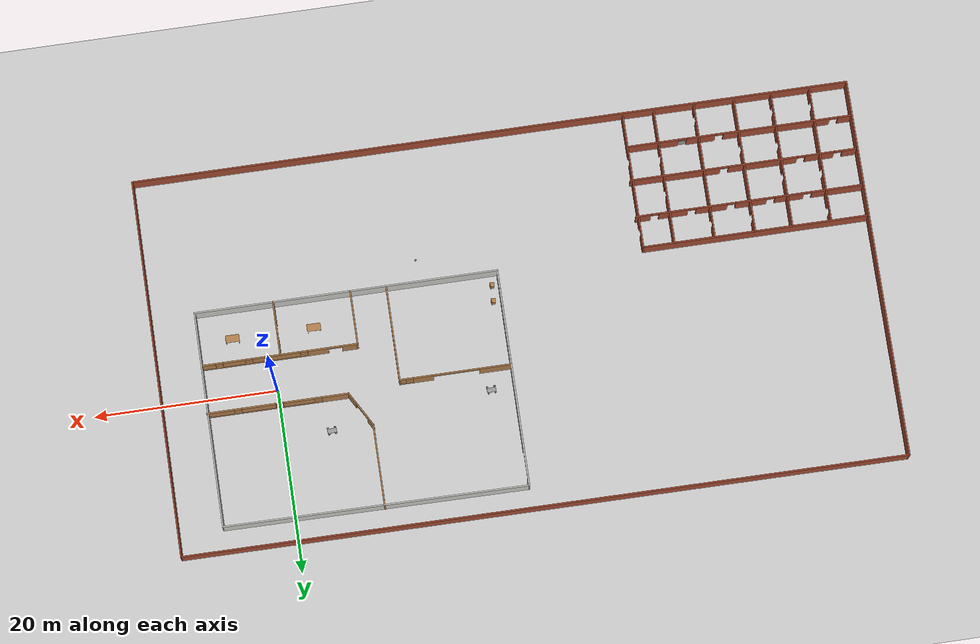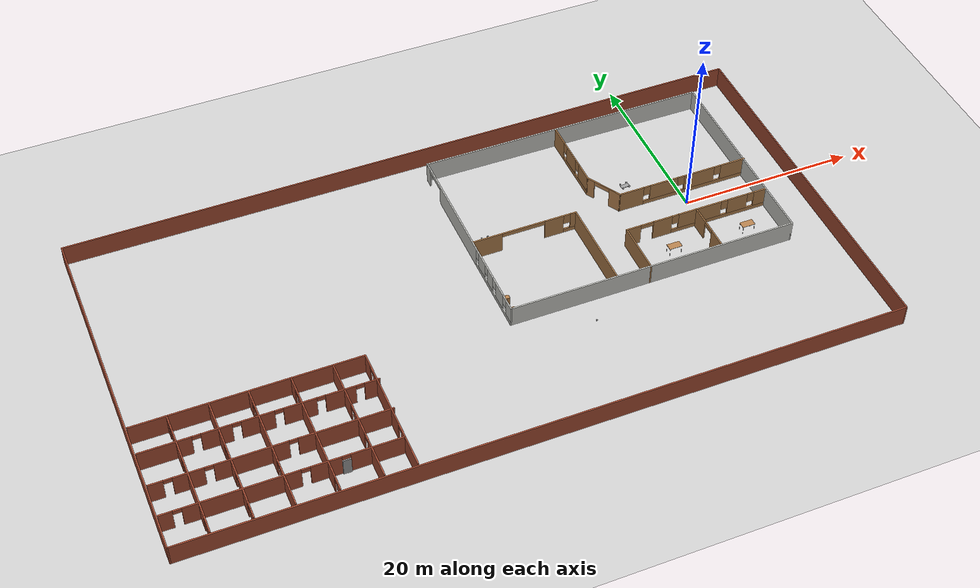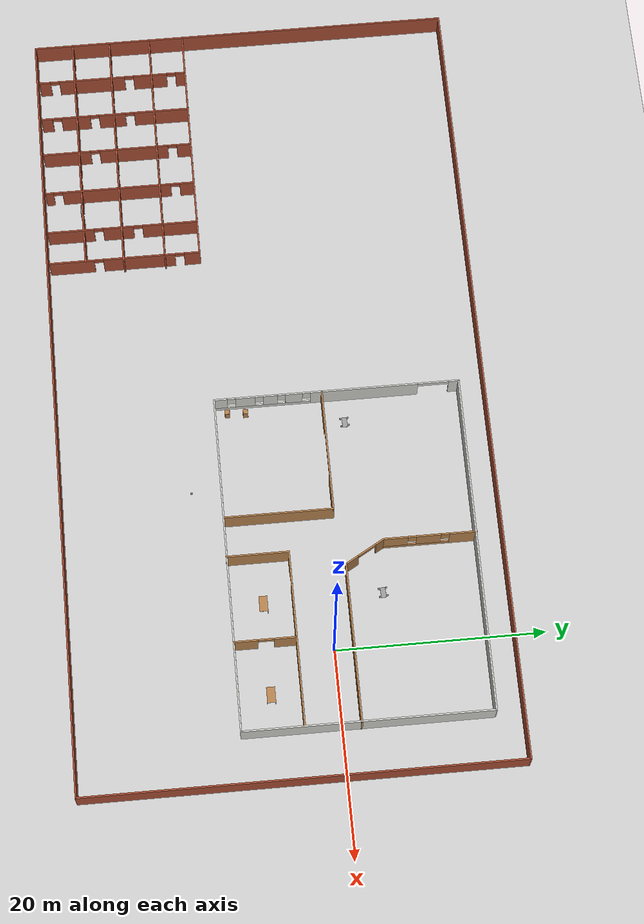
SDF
<sdf version="1.6">
 <world name="default">
  <plugin name="welcome" filename="libwelcome.so"/>
  <light name="sun" type="directional">
   <pose>0 0 10 0 -0 0</pose>
   <diffuse>0.8 0.8 0.8 1</diffuse>
   <specular>0.2 0.2 0.2 1</specular>
   <attenuation>
    <range>1000</range>
    <constant>0.9</constant>
    <linear>0.01</linear>
    <quadratic>0.001</quadratic>
   </attenuation>
   <direction>-0.5 0.1 -0.9</direction>
  </light>
  <model name="ground_plane">
   <static>1</static>
   <link name="link">
    <collision name="collision">
     <geometry><plane><normal>0 0 1</normal><size>100 100</size></plane></geometry>
     <surface>
      <contact><collide_bitmask>65535</collide_bitmask></contact>
      <friction><ode><mu>100</mu><mu2>50</mu2></ode></friction>
     </surface>
    </collision>
    <visual name="visual">
     <cast_shadows>0</cast_shadows>
     <geometry><plane><normal>0 0 1</normal><size>100 100</size></plane></geometry>
     <material>
      <script><uri>file://media/materials/scripts/gazebo.material</uri><name>Gazebo/Grey</name></script>
     </material>
    </visual>
   </link>
  </model>
  <gravity>0 0 -9.8</gravity>
  <magnetic_field>6e-06 2.3e-05 -4.2e-05</magnetic_field>
  <atmosphere type="adiabatic"/>
  <physics name="default_physics" default="0" type="ode">
   <max_step_size>0.001</max_step_size>
   <real_time_factor>1</real_time_factor>
   <real_time_update_rate>1000</real_time_update_rate>
  </physics>
  <scene><ambient>0.4 0.4 0.4 1</ambient><background>0.7 0.7 0.7 1</background><shadows>1</shadows></scene>
  <spherical_coordinates>
   <surface_model>EARTH_WGS84</surface_model>
   <latitude_deg>0</latitude_deg>
   <longitude_deg>0</longitude_deg>
   <elevation>0</elevation>
   <heading_deg>0</heading_deg>
  </spherical_coordinates>
  <model name="bigHouse">
   <pose>-26.8831 -3.8622 0 0 -0 0</pose>
   <link name="Door_24">
    <collision name="Door_24_Collision">
     <geometry><box><size>0.9 0.17 2</size></box></geometry>
     <pose>0 0 1 0 -0 0</pose>
    </collision>
    <visual name="Door_24_Visual">
     <pose>0 0 1 0 -0 0</pose>
     <geometry><box><size>0.9 0.17 2</size></box></geometry>
     <material>
      <script><uri>file://media/materials/scripts/gazebo.material</uri><name>Gazebo/Grey</name></script>
     </material>
    </visual>
    <pose>-20.6544 -17.2138 0 0 -0 0</pose>
   </link>
   <link name="Wall_0">
    <collision name="Wall_0_Collision">
     <geometry><box><size>42 0.15 2.5</size></box></geometry>
     <pose>0 0 1.25 0 -0 0</pose>
    </collision>
    <visual name="Wall_0_Visual">
     <pose>0 0 1.25 0 -0 0</pose>
     <geometry><box><size>42 0.15 2.5</size></box></geometry>
     <material>
      <script><uri>file://media/materials/scripts/gazebo.material</uri><name>Gazebo/Bricks</name></script>
      <ambient>1 1 1 1</ambient>
     </material>
     <meta><layer>0</layer></meta>
    </visual>
    <pose>-39.425 -0.000117 0 0 0 -1.5708</pose>
   </link>
   <link name="Wall_1">
    <collision name="Wall_1_Collision">
     <geometry><box><size>79 0.15 2.5</size></box></geometry>
     <pose>0 0 1.25 0 -0 0</pose>
    </collision>
    <visual name="Wall_1_Visual">
     <pose>0 0 1.25 0 -0 0</pose>
     <geometry><box><size>79 0.15 2.5</size></box></geometry>
     <material>
      <script><uri>file://media/materials/scripts/gazebo.material</uri><name>Gazebo/Bricks</name></script>
      <ambient>1 1 1 1</ambient>
     </material>
     <meta><layer>0</layer></meta>
    </visual>
    <pose>1e-06 -20.9251 0 0 -0 0</pose>
   </link>
   <link name="Wall_10">
    <pose>7.59462 4.97423 0 0 -0 0</pose>
    <visual name="Wall_10_Visual_0">
     <pose>-4.3849 0 1.25 0 -0 0</pose>
     <geometry><box><size>3.48019 0.15 2.5</size></box></geometry>
     <material>
      <script><uri>file://media/materials/scripts/gazebo.material</uri><name>Gazebo/Wood</name></script>
      <ambient>1 1 1 1</ambient>
     </material>
     <meta><layer>0</layer></meta>
    </visual>
    <collision name="Wall_10_Collision_0">
     <geometry><box><size>3.48019 0.15 2.5</size></box></geometry>
     <pose>-4.3849 0 1.25 0 -0 0</pose>
    </collision>
    <visual name="Wall_10_Visual_1">
     <pose>3.45765 0 1.25 0 -0 0</pose>
     <geometry><box><size>2.20491 0.15 2.5</size></box></geometry>
     <material>
      <script><uri>file://media/materials/scripts/gazebo.material</uri><name>Gazebo/Wood</name></script>
      <ambient>1 1 1 1</ambient>
     </material>
     <meta><layer>0</layer></meta>
    </visual>
    <collision name="Wall_10_Collision_1">
     <geometry><box><size>2.20491 0.15 2.5</size></box></geometry>
     <pose>3.45765 0 1.25 0 -0 0</pose>
    </collision>
    <visual name="Wall_10_Visual_2">
     <pose>5.34255 0 0.25 0 -0 0</pose>
     <geometry><box><size>1.56489 0.15 0.5</size></box></geometry>
     <material>
      <script><uri>file://media/materials/scripts/gazebo.material</uri><name>Gazebo/Wood</name></script>
      <ambient>1 1 1 1</ambient>
     </material>
     <meta><layer>0</layer></meta>
    </visual>
    <collision name="Wall_10_Collision_2">
     <geometry><box><size>1.56489 0.15 0.5</size></box></geometry>
     <pose>5.34255 0 0.25 0 -0 0</pose>
    </collision>
    <visual name="Wall_10_Visual_3">
     <pose>5.74255 0 1.5 0 -0 0</pose>
     <geometry><box><size>0.764895 0.15 2</size></box></geometry>
     <material>
      <script><uri>file://media/materials/scripts/gazebo.material</uri><name>Gazebo/Wood</name></script>
      <ambient>1 1 1 1</ambient>
     </material>
     <meta><layer>0</layer></meta>
    </visual>
    <collision name="Wall_10_Collision_3">
     <geometry><box><size>0.764895 0.15 2</size></box></geometry>
     <pose>5.74255 0 1.5 0 -0 0</pose>
    </collision>
    <visual name="Wall_10_Visual_4">
     <pose>4.96011 0 1.9 0 -0 0</pose>
     <geometry><box><size>0.8 0.15 1.2</size></box></geometry>
     <material>
      <script><uri>file://media/materials/scripts/gazebo.material</uri><name>Gazebo/Wood</name></script>
      <ambient>1 1 1 1</ambient>
     </material>
     <meta><layer>0</layer></meta>
    </visual>
    <collision name="Wall_10_Collision_4">
     <geometry><box><size>0.8 0.15 1.2</size></box></geometry>
     <pose>4.96011 0 1.9 0 -0 0</pose>
    </collision>
    <visual name="Wall_10_Visual_5">
     <pose>-0.144808 0 2.25 0 -0 0</pose>
     <geometry><box><size>5 0.15 0.5</size></box></geometry>
     <material>
      <script><uri>file://media/materials/scripts/gazebo.material</uri><name>Gazebo/Wood</name></script>
      <ambient>1 1 1 1</ambient>
     </material>
     <meta><layer>0</layer></meta>
    </visual>
    <collision name="Wall_10_Collision_5">
     <geometry><box><size>5 0.15 0.5</size></box></geometry>
     <pose>-0.144808 0 2.25 0 -0 0</pose>
    </collision>
   </link>
   <link name="Wall_11">
    <collision name="Wall_11_Collision">
     <geometry><box><size>10.5 0.15 2.5</size></box></geometry>
     <pose>0 0 1.25 0 -0 0</pose>
    </collision>
    <visual name="Wall_11_Visual">
     <pose>0 0 1.25 0 -0 0</pose>
     <geometry><box><size>10.5 0.15 2.5</size></box></geometry>
     <material>
      <script><uri>file://media/materials/scripts/gazebo.material</uri><name>Gazebo/Wood</name></script>
      <ambient>1 1 1 1</ambient>
     </material>
     <meta><layer>0</layer></meta>
    </visual>
    <pose>13.6446 -0.200766 0 0 0 -1.5708</pose>
   </link>
   <link name="Wall_13">
    <pose>26.0111 0.377542 0 0 -0 0</pose>
    <visual name="Wall_13_Visual_0">
     <pose>-7.61414 0 1.25 0 -0 0</pose>
     <geometry><box><size>1.77173 0.15 2.5</size></box></geometry>
     <material>
      <script><uri>file://media/materials/scripts/gazebo.material</uri><name>Gazebo/Wood</name></script>
      <ambient>1 1 1 1</ambient>
     </material>
     <meta><layer>0</layer></meta>
    </visual>
    <collision name="Wall_13_Collision_0">
     <geometry><box><size>1.77173 0.15 2.5</size></box></geometry>
     <pose>-7.61414 0 1.25 0 -0 0</pose>
    </collision>
    <visual name="Wall_13_Visual_1">
     <pose>-4.09432 0 1.25 0 -0 0</pose>
     <geometry><box><size>2.2679 0.15 2.5</size></box></geometry>
     <material>
      <script><uri>file://media/materials/scripts/gazebo.material</uri><name>Gazebo/Wood</name></script>
      <ambient>1 1 1 1</ambient>
     </material>
     <meta><layer>0</layer></meta>
    </visual>
    <collision name="Wall_13_Collision_1">
     <geometry><box><size>2.2679 0.15 2.5</size></box></geometry>
     <pose>-4.09432 0 1.25 0 -0 0</pose>
    </collision>
    <visual name="Wall_13_Visual_2">
     <pose>2.76981 0 0.25 0 -0 0</pose>
     <geometry><box><size>11.4604 0.15 0.5</size></box></geometry>
     <material>
      <script><uri>file://media/materials/scripts/gazebo.material</uri><name>Gazebo/Wood</name></script>
      <ambient>1 1 1 1</ambient>
     </material>
     <meta><layer>0</layer></meta>
    </visual>
    <collision name="Wall_13_Collision_2">
     <geometry><box><size>11.4604 0.15 0.5</size></box></geometry>
     <pose>2.76981 0 0.25 0 -0 0</pose>
    </collision>
    <visual name="Wall_13_Visual_3">
     <pose>0.433338 0 1.5 0 -0 0</pose>
     <geometry><box><size>5.18743 0.15 2</size></box></geometry>
     <material>
      <script><uri>file://media/materials/scripts/gazebo.material</uri><name>Gazebo/Wood</name></script>
      <ambient>1 1 1 1</ambient>
     </material>
     <meta><layer>0</layer></meta>
    </visual>
    <collision name="Wall_13_Collision_3">
     <geometry><box><size>5.18743 0.15 2</size></box></geometry>
     <pose>0.433338 0 1.5 0 -0 0</pose>
    </collision>
    <visual name="Wall_13_Visual_4">
     <pose>5.04527 0 1.5 0 -0 0</pose>
     <geometry><box><size>2.43645 0.15 2</size></box></geometry>
     <material>
      <script><uri>file://media/materials/scripts/gazebo.material</uri><name>Gazebo/Wood</name></script>
      <ambient>1 1 1 1</ambient>
     </material>
     <meta><layer>0</layer></meta>
    </visual>
    <collision name="Wall_13_Collision_4">
     <geometry><box><size>2.43645 0.15 2</size></box></geometry>
     <pose>5.04527 0 1.5 0 -0 0</pose>
    </collision>
    <visual name="Wall_13_Visual_5">
     <pose>7.78175 0 1.5 0 -0 0</pose>
     <geometry><box><size>1.4365 0.15 2</size></box></geometry>
     <material>
      <script><uri>file://media/materials/scripts/gazebo.material</uri><name>Gazebo/Wood</name></script>
      <ambient>1 1 1 1</ambient>
     </material>
     <meta><layer>0</layer></meta>
    </visual>
    <collision name="Wall_13_Collision_5">
     <geometry><box><size>1.4365 0.15 2</size></box></geometry>
     <pose>7.78175 0 1.5 0 -0 0</pose>
    </collision>
    <visual name="Wall_13_Visual_6">
     <pose>-2.56038 0 1.9 0 -0 0</pose>
     <geometry><box><size>0.8 0.15 1.2</size></box></geometry>
     <material>
      <script><uri>file://media/materials/scripts/gazebo.material</uri><name>Gazebo/Wood</name></script>
      <ambient>1 1 1 1</ambient>
     </material>
     <meta><layer>0</layer></meta>
    </visual>
    <collision name="Wall_13_Collision_6">
     <geometry><box><size>0.8 0.15 1.2</size></box></geometry>
     <pose>-2.56038 0 1.9 0 -0 0</pose>
    </collision>
    <visual name="Wall_13_Visual_7">
     <pose>3.42705 0 1.9 0 -0 0</pose>
     <geometry><box><size>0.8 0.15 1.2</size></box></geometry>
     <material>
      <script><uri>file://media/materials/scripts/gazebo.material</uri><name>Gazebo/Wood</name></script>
      <ambient>1 1 1 1</ambient>
     </material>
     <meta><layer>0</layer></meta>
    </visual>
    <collision name="Wall_13_Collision_7">
     <geometry><box><size>0.8 0.15 1.2</size></box></geometry>
     <pose>3.42705 0 1.9 0 -0 0</pose>
    </collision>
    <visual name="Wall_13_Visual_8">
     <pose>6.6635 0 1.9 0 -0 0</pose>
     <geometry><box><size>0.8 0.15 1.2</size></box></geometry>
     <material>
      <script><uri>file://media/materials/scripts/gazebo.material</uri><name>Gazebo/Wood</name></script>
      <ambient>1 1 1 1</ambient>
     </material>
     <meta><layer>0</layer></meta>
    </visual>
    <collision name="Wall_13_Collision_8">
     <geometry><box><size>0.8 0.15 1.2</size></box></geometry>
     <pose>6.6635 0 1.9 0 -0 0</pose>
    </collision>
    <visual name="Wall_13_Visual_9">
     <pose>-5.97827 0 2.25 0 -0 0</pose>
     <geometry><box><size>1.5 0.15 0.5</size></box></geometry>
     <material>
      <script><uri>file://media/materials/scripts/gazebo.material</uri><name>Gazebo/Wood</name></script>
      <ambient>1 1 1 1</ambient>
     </material>
     <meta><layer>0</layer></meta>
    </visual>
    <collision name="Wall_13_Collision_9">
     <geometry><box><size>1.5 0.15 0.5</size></box></geometry>
     <pose>-5.97827 0 2.25 0 -0 0</pose>
    </collision>
   </link>
   <link name="Wall_15">
    <collision name="Wall_15_Collision">
     <geometry><box><size>6.06003 0.15 2.5</size></box></geometry>
     <pose>0 0 1.25 0 -0 0</pose>
    </collision>
    <visual name="Wall_15_Visual">
     <pose>0 0 1.25 0 -0 0</pose>
     <geometry><box><size>6.06003 0.15 2.5</size></box></geometry>
     <material>
      <script><uri>file://media/materials/scripts/gazebo.material</uri><name>Gazebo/Wood</name></script>
      <ambient>1 1 1 1</ambient>
     </material>
     <meta><layer>0</layer></meta>
    </visual>
    <pose>17.5861 -2.57747 0 0 -0 1.5708</pose>
   </link>
   <link name="Wall_17">
    <pose>17.1284 13.8352 0 0 0 -1.5708</pose>
    <visual name="Wall_17_Visual_0">
     <pose>-3.18124 0 1.25 0 -0 0</pose>
     <geometry><box><size>2.63752 0.15 2.5</size></box></geometry>
     <material>
      <script><uri>file://media/materials/scripts/gazebo.material</uri><name>Gazebo/Wood</name></script>
      <ambient>1 1 1 1</ambient>
     </material>
     <meta><layer>0</layer></meta>
    </visual>
    <collision name="Wall_17_Collision_0">
     <geometry><box><size>2.63752 0.15 2.5</size></box></geometry>
     <pose>-3.18124 0 1.25 0 -0 0</pose>
    </collision>
    <visual name="Wall_17_Visual_1">
     <pose>1.31876 0 0.25 0 -0 0</pose>
     <geometry><box><size>6.36248 0.15 0.5</size></box></geometry>
     <material>
      <script><uri>file://media/materials/scripts/gazebo.material</uri><name>Gazebo/Wood</name></script>
      <ambient>1 1 1 1</ambient>
     </material>
     <meta><layer>0</layer></meta>
    </visual>
    <collision name="Wall_17_Collision_1">
     <geometry><box><size>6.36248 0.15 0.5</size></box></geometry>
     <pose>1.31876 0 0.25 0 -0 0</pose>
    </collision>
    <visual name="Wall_17_Visual_2">
     <pose>0.110682 0 1.5 0 -0 0</pose>
     <geometry><box><size>2.34633 0.15 2</size></box></geometry>
     <material>
      <script><uri>file://media/materials/scripts/gazebo.material</uri><name>Gazebo/Wood</name></script>
      <ambient>1 1 1 1</ambient>
     </material>
     <meta><layer>0</layer></meta>
    </visual>
    <collision name="Wall_17_Collision_2">
     <geometry><box><size>2.34633 0.15 2</size></box></geometry>
     <pose>0.110682 0 1.5 0 -0 0</pose>
    </collision>
    <visual name="Wall_17_Visual_3">
     <pose>3.29192 0 1.5 0 -0 0</pose>
     <geometry><box><size>2.41615 0.15 2</size></box></geometry>
     <material>
      <script><uri>file://media/materials/scripts/gazebo.material</uri><name>Gazebo/Wood</name></script>
      <ambient>1 1 1 1</ambient>
     </material>
     <meta><layer>0</layer></meta>
    </visual>
    <collision name="Wall_17_Collision_3">
     <geometry><box><size>2.41615 0.15 2</size></box></geometry>
     <pose>3.29192 0 1.5 0 -0 0</pose>
    </collision>
    <visual name="Wall_17_Visual_4">
     <pose>-1.46248 0 1.9 0 -0 0</pose>
     <geometry><box><size>0.8 0.15 1.2</size></box></geometry>
     <material>
      <script><uri>file://media/materials/scripts/gazebo.material</uri><name>Gazebo/Wood</name></script>
      <ambient>1 1 1 1</ambient>
     </material>
     <meta><layer>0</layer></meta>
    </visual>
    <collision name="Wall_17_Collision_4">
     <geometry><box><size>0.8 0.15 1.2</size></box></geometry>
     <pose>-1.46248 0 1.9 0 -0 0</pose>
    </collision>
    <visual name="Wall_17_Visual_5">
     <pose>1.68385 0 1.9 0 -0 0</pose>
     <geometry><box><size>0.8 0.15 1.2</size></box></geometry>
     <material>
      <script><uri>file://media/materials/scripts/gazebo.material</uri><name>Gazebo/Wood</name></script>
      <ambient>1 1 1 1</ambient>
     </material>
     <meta><layer>0</layer></meta>
    </visual>
    <collision name="Wall_17_Collision_5">
     <geometry><box><size>0.8 0.15 1.2</size></box></geometry>
     <pose>1.68385 0 1.9 0 -0 0</pose>
    </collision>
   </link>
   <link name="Wall_18">
    <pose>18.2159 7.5266 0 0 0 -1.0472</pose>
    <visual name="Wall_18_Visual_0">
     <pose>-1.74861 0 1.25 0 -0 0</pose>
     <geometry><box><size>1.00278 0.15 2.5</size></box></geometry>
     <material>
      <script><uri>file://media/materials/scripts/gazebo.material</uri><name>Gazebo/Wood</name></script>
      <ambient>1 1 1 1</ambient>
     </material>
     <meta><layer>0</layer></meta>
    </visual>
    <collision name="Wall_18_Collision_0">
     <geometry><box><size>1.00278 0.15 2.5</size></box></geometry>
     <pose>-1.74861 0 1.25 0 -0 0</pose>
    </collision>
    <visual name="Wall_18_Visual_1">
     <pose>1.50139 0 1.25 0 -0 0</pose>
     <geometry><box><size>1.49722 0.15 2.5</size></box></geometry>
     <material>
      <script><uri>file://media/materials/scripts/gazebo.material</uri><name>Gazebo/Wood</name></script>
      <ambient>1 1 1 1</ambient>
     </material>
     <meta><layer>0</layer></meta>
    </visual>
    <collision name="Wall_18_Collision_1">
     <geometry><box><size>1.49722 0.15 2.5</size></box></geometry>
     <pose>1.50139 0 1.25 0 -0 0</pose>
    </collision>
    <visual name="Wall_18_Visual_2">
     <pose>-0.247217 0 2.25 0 -0 0</pose>
     <geometry><box><size>2 0.15 0.5</size></box></geometry>
     <material>
      <script><uri>file://media/materials/scripts/gazebo.material</uri><name>Gazebo/Wood</name></script>
      <ambient>1 1 1 1</ambient>
     </material>
     <meta><layer>0</layer></meta>
    </visual>
    <collision name="Wall_18_Collision_2">
     <geometry><box><size>2 0.15 0.5</size></box></geometry>
     <pose>-0.247217 0 2.25 0 -0 0</pose>
    </collision>
   </link>
   <link name="Wall_19">
    <pose>26.9784 5.643 0 0 -0 0</pose>
    <visual name="Wall_19_Visual_0">
     <pose>-6.27032 0 1.25 0 -0 0</pose>
     <geometry><box><size>2.95935 0.15 2.5</size></box></geometry>
     <material>
      <script><uri>file://media/materials/scripts/gazebo.material</uri><name>Gazebo/Wood</name></script>
      <ambient>1 1 1 1</ambient>
     </material>
     <meta><layer>0</layer></meta>
    </visual>
    <collision name="Wall_19_Collision_0">
     <geometry><box><size>2.95935 0.15 2.5</size></box></geometry>
     <pose>-6.27032 0 1.25 0 -0 0</pose>
    </collision>
    <visual name="Wall_19_Visual_1">
     <pose>1.47968 0 0.25 0 -0 0</pose>
     <geometry><box><size>12.5406 0.15 0.5</size></box></geometry>
     <material>
      <script><uri>file://media/materials/scripts/gazebo.material</uri><name>Gazebo/Wood</name></script>
      <ambient>1 1 1 1</ambient>
     </material>
     <meta><layer>0</layer></meta>
    </visual>
    <collision name="Wall_19_Collision_1">
     <geometry><box><size>12.5406 0.15 0.5</size></box></geometry>
     <pose>1.47968 0 0.25 0 -0 0</pose>
    </collision>
    <visual name="Wall_19_Visual_2">
     <pose>-2.28696 0 1.5 0 -0 0</pose>
     <geometry><box><size>3.40738 0.15 2</size></box></geometry>
     <material>
      <script><uri>file://media/materials/scripts/gazebo.material</uri><name>Gazebo/Wood</name></script>
      <ambient>1 1 1 1</ambient>
     </material>
     <meta><layer>0</layer></meta>
    </visual>
    <collision name="Wall_19_Collision_2">
     <geometry><box><size>3.40738 0.15 2</size></box></geometry>
     <pose>-2.28696 0 1.5 0 -0 0</pose>
    </collision>
    <visual name="Wall_19_Visual_3">
     <pose>2.08224 0 1.5 0 -0 0</pose>
     <geometry><box><size>3.73102 0.15 2</size></box></geometry>
     <material>
      <script><uri>file://media/materials/scripts/gazebo.material</uri><name>Gazebo/Wood</name></script>
      <ambient>1 1 1 1</ambient>
     </material>
     <meta><layer>0</layer></meta>
    </visual>
    <collision name="Wall_19_Collision_3">
     <geometry><box><size>3.73102 0.15 2</size></box></geometry>
     <pose>2.08224 0 1.5 0 -0 0</pose>
    </collision>
    <visual name="Wall_19_Visual_4">
     <pose>6.24888 0 1.5 0 -0 0</pose>
     <geometry><box><size>3.00224 0.15 2</size></box></geometry>
     <material>
      <script><uri>file://media/materials/scripts/gazebo.material</uri><name>Gazebo/Wood</name></script>
      <ambient>1 1 1 1</ambient>
     </material>
     <meta><layer>0</layer></meta>
    </visual>
    <collision name="Wall_19_Collision_4">
     <geometry><box><size>3.00224 0.15 2</size></box></geometry>
     <pose>6.24888 0 1.5 0 -0 0</pose>
    </collision>
    <visual name="Wall_19_Visual_5">
     <pose>-4.39065 0 1.9 0 -0 0</pose>
     <geometry><box><size>0.8 0.15 1.2</size></box></geometry>
     <material>
      <script><uri>file://media/materials/scripts/gazebo.material</uri><name>Gazebo/Wood</name></script>
      <ambient>1 1 1 1</ambient>
     </material>
     <meta><layer>0</layer></meta>
    </visual>
    <collision name="Wall_19_Collision_5">
     <geometry><box><size>0.8 0.15 1.2</size></box></geometry>
     <pose>-4.39065 0 1.9 0 -0 0</pose>
    </collision>
    <visual name="Wall_19_Visual_6">
     <pose>-0.183267 0 1.9 0 -0 0</pose>
     <geometry><box><size>0.8 0.15 1.2</size></box></geometry>
     <material>
      <script><uri>file://media/materials/scripts/gazebo.material</uri><name>Gazebo/Wood</name></script>
      <ambient>1 1 1 1</ambient>
     </material>
     <meta><layer>0</layer></meta>
    </visual>
    <collision name="Wall_19_Collision_6">
     <geometry><box><size>0.8 0.15 1.2</size></box></geometry>
     <pose>-0.183267 0 1.9 0 -0 0</pose>
    </collision>
    <visual name="Wall_19_Visual_7">
     <pose>4.34776 0 1.9 0 -0 0</pose>
     <geometry><box><size>0.8 0.15 1.2</size></box></geometry>
     <material>
      <script><uri>file://media/materials/scripts/gazebo.material</uri><name>Gazebo/Wood</name></script>
      <ambient>1 1 1 1</ambient>
     </material>
     <meta><layer>0</layer></meta>
    </visual>
    <collision name="Wall_19_Collision_7">
     <geometry><box><size>0.8 0.15 1.2</size></box></geometry>
     <pose>4.34776 0 1.9 0 -0 0</pose>
    </collision>
   </link>
   <link name="Wall_2">
    <collision name="Wall_2_Collision">
     <geometry><box><size>41.75 0.15 2.5</size></box></geometry>
     <pose>0 0 1.25 0 -0 0</pose>
    </collision>
    <visual name="Wall_2_Visual">
     <pose>0 0 1.25 0 -0 0</pose>
     <geometry><box><size>41.75 0.15 2.5</size></box></geometry>
     <material>
      <script><uri>file://media/materials/scripts/gazebo.material</uri><name>Gazebo/Bricks</name></script>
      <ambient>1 1 1 1</ambient>
     </material>
     <meta><layer>0</layer></meta>
    </visual>
    <pose>39.425 -0.125117 0 0 -0 1.5708</pose>
   </link>
   <link name="Wall_21">
    <pose>26.016 -2.57919 0 0 0 -1.5708</pose>
    <visual name="Wall_21_Visual_0">
     <pose>-1.91882 0 1.25 0 -0 0</pose>
     <geometry><box><size>2.16235 0.15 2.5</size></box></geometry>
     <material>
      <script><uri>file://media/materials/scripts/gazebo.material</uri><name>Gazebo/Wood</name></script>
      <ambient>1 1 1 1</ambient>
     </material>
     <meta><layer>0</layer></meta>
    </visual>
    <collision name="Wall_21_Collision_0">
     <geometry><box><size>2.16235 0.15 2.5</size></box></geometry>
     <pose>-1.91882 0 1.25 0 -0 0</pose>
    </collision>
    <visual name="Wall_21_Visual_1">
     <pose>1.83118 0 1.25 0 -0 0</pose>
     <geometry><box><size>2.33765 0.15 2.5</size></box></geometry>
     <material>
      <script><uri>file://media/materials/scripts/gazebo.material</uri><name>Gazebo/Wood</name></script>
      <ambient>1 1 1 1</ambient>
     </material>
     <meta><layer>0</layer></meta>
    </visual>
    <collision name="Wall_21_Collision_1">
     <geometry><box><size>2.33765 0.15 2.5</size></box></geometry>
     <pose>1.83118 0 1.25 0 -0 0</pose>
    </collision>
    <visual name="Wall_21_Visual_2">
     <pose>-0.087646 0 2.25 0 -0 0</pose>
     <geometry><box><size>1.5 0.15 0.5</size></box></geometry>
     <material>
      <script><uri>file://media/materials/scripts/gazebo.material</uri><name>Gazebo/Wood</name></script>
      <ambient>1 1 1 1</ambient>
     </material>
     <meta><layer>0</layer></meta>
    </visual>
    <collision name="Wall_21_Collision_2">
     <geometry><box><size>1.5 0.15 0.5</size></box></geometry>
     <pose>-0.087646 0 2.25 0 -0 0</pose>
    </collision>
   </link>
   <link name="Wall_23">
    <collision name="Wall_23_Collision">
     <geometry><box><size>24.75 0.15 2.5</size></box></geometry>
     <pose>0 0 1.25 0 -0 0</pose>
    </collision>
    <visual name="Wall_23_Visual">
     <pose>0 0 1.25 0 -0 0</pose>
     <geometry><box><size>24.75 0.15 2.5</size></box></geometry>
     <material>
      <script><uri>file://media/materials/scripts/gazebo.material</uri><name>Gazebo/Bricks</name></script>
      <ambient>1 1 1 1</ambient>
     </material>
     <meta><layer>0</layer></meta>
    </visual>
    <pose>-26.9069 -5.76164 0 0 -0 0</pose>
   </link>
   <link name="Wall_24">
    <pose>-14.6069 -13.1866 0 0 0 -1.5708</pose>
    <visual name="Wall_24_Visual_0">
     <pose>-6.69597 0 1.25 0 -0 0</pose>
     <geometry><box><size>1.60807 0.15 2.5</size></box></geometry>
     <material>
      <script><uri>file://media/materials/scripts/gazebo.material</uri><name>Gazebo/Bricks</name></script>
      <ambient>1 1 1 1</ambient>
     </material>
     <meta><layer>0</layer></meta>
    </visual>
    <collision name="Wall_24_Collision_0">
     <geometry><box><size>1.60807 0.15 2.5</size></box></geometry>
     <pose>-6.69597 0 1.25 0 -0 0</pose>
    </collision>
    <visual name="Wall_24_Visual_1">
     <pose>-1.42211 0 1.25 0 -0 0</pose>
     <geometry><box><size>7.13964 0.15 2.5</size></box></geometry>
     <material>
      <script><uri>file://media/materials/scripts/gazebo.material</uri><name>Gazebo/Bricks</name></script>
      <ambient>1 1 1 1</ambient>
     </material>
     <meta><layer>0</layer></meta>
    </visual>
    <collision name="Wall_24_Collision_1">
     <geometry><box><size>7.13964 0.15 2.5</size></box></geometry>
     <pose>-1.42211 0 1.25 0 -0 0</pose>
    </collision>
    <visual name="Wall_24_Visual_2">
     <pose>5.27386 0 1.25 0 -0 0</pose>
     <geometry><box><size>4.45229 0.15 2.5</size></box></geometry>
     <material>
      <script><uri>file://media/materials/scripts/gazebo.material</uri><name>Gazebo/Bricks</name></script>
      <ambient>1 1 1 1</ambient>
     </material>
     <meta><layer>0</layer></meta>
    </visual>
    <collision name="Wall_24_Collision_2">
     <geometry><box><size>4.45229 0.15 2.5</size></box></geometry>
     <pose>5.27386 0 1.25 0 -0 0</pose>
    </collision>
    <visual name="Wall_24_Visual_3">
     <pose>-5.44193 0 2.25 0 -0 0</pose>
     <geometry><box><size>0.9 0.15 0.5</size></box></geometry>
     <material>
      <script><uri>file://media/materials/scripts/gazebo.material</uri><name>Gazebo/Bricks</name></script>
      <ambient>1 1 1 1</ambient>
     </material>
     <meta><layer>0</layer></meta>
    </visual>
    <collision name="Wall_24_Collision_3">
     <geometry><box><size>0.9 0.15 0.5</size></box></geometry>
     <pose>-5.44193 0 2.25 0 -0 0</pose>
    </collision>
    <visual name="Wall_24_Visual_4">
     <pose>2.59771 0 2.25 0 -0 0</pose>
     <geometry><box><size>0.9 0.15 0.5</size></box></geometry>
     <material>
      <script><uri>file://media/materials/scripts/gazebo.material</uri><name>Gazebo/Bricks</name></script>
      <ambient>1 1 1 1</ambient>
     </material>
     <meta><layer>0</layer></meta>
    </visual>
    <collision name="Wall_24_Collision_4">
     <geometry><box><size>0.9 0.15 0.5</size></box></geometry>
     <pose>2.59771 0 2.25 0 -0 0</pose>
    </collision>
   </link>
   <link name="Wall_26">
    <pose>-35.2751 -13.2008 0 0 0 -1.5708</pose>
    <visual name="Wall_26_Visual_0">
     <pose>-6.97508 0 1.25 0 -0 0</pose>
     <geometry><box><size>1.04984 0.15 2.5</size></box></geometry>
     <material>
      <script><uri>file://media/materials/scripts/gazebo.material</uri><name>Gazebo/Bricks</name></script>
      <ambient>1 1 1 1</ambient>
     </material>
     <meta><layer>0</layer></meta>
    </visual>
    <collision name="Wall_26_Collision_0">
     <geometry><box><size>1.04984 0.15 2.5</size></box></geometry>
     <pose>-6.97508 0 1.25 0 -0 0</pose>
    </collision>
    <visual name="Wall_26_Visual_1">
     <pose>-3.83887 0 1.25 0 -0 0</pose>
     <geometry><box><size>3.42259 0.15 2.5</size></box></geometry>
     <material>
      <script><uri>file://media/materials/scripts/gazebo.material</uri><name>Gazebo/Bricks</name></script>
      <ambient>1 1 1 1</ambient>
     </material>
     <meta><layer>0</layer></meta>
    </visual>
    <collision name="Wall_26_Collision_1">
     <geometry><box><size>3.42259 0.15 2.5</size></box></geometry>
     <pose>-3.83887 0 1.25 0 -0 0</pose>
    </collision>
    <visual name="Wall_26_Visual_2">
     <pose>2.12345 0 1.25 0 -0 0</pose>
     <geometry><box><size>6.70206 0.15 2.5</size></box></geometry>
     <material>
      <script><uri>file://media/materials/scripts/gazebo.material</uri><name>Gazebo/Bricks</name></script>
      <ambient>1 1 1 1</ambient>
     </material>
     <meta><layer>0</layer></meta>
    </visual>
    <collision name="Wall_26_Collision_2">
     <geometry><box><size>6.70206 0.15 2.5</size></box></geometry>
     <pose>2.12345 0 1.25 0 -0 0</pose>
    </collision>
    <visual name="Wall_26_Visual_3">
     <pose>6.93724 0 1.25 0 -0 0</pose>
     <geometry><box><size>1.12552 0.15 2.5</size></box></geometry>
     <material>
      <script><uri>file://media/materials/scripts/gazebo.material</uri><name>Gazebo/Bricks</name></script>
      <ambient>1 1 1 1</ambient>
     </material>
     <meta><layer>0</layer></meta>
    </visual>
    <collision name="Wall_26_Collision_3">
     <geometry><box><size>1.12552 0.15 2.5</size></box></geometry>
     <pose>6.93724 0 1.25 0 -0 0</pose>
    </collision>
    <visual name="Wall_26_Visual_4">
     <pose>-6.00016 0 2.25 0 -0 0</pose>
     <geometry><box><size>0.9 0.15 0.5</size></box></geometry>
     <material>
      <script><uri>file://media/materials/scripts/gazebo.material</uri><name>Gazebo/Bricks</name></script>
      <ambient>1 1 1 1</ambient>
     </material>
     <meta><layer>0</layer></meta>
    </visual>
    <collision name="Wall_26_Collision_4">
     <geometry><box><size>0.9 0.15 0.5</size></box></geometry>
     <pose>-6.00016 0 2.25 0 -0 0</pose>
    </collision>
    <visual name="Wall_26_Visual_5">
     <pose>-1.67757 0 2.25 0 -0 0</pose>
     <geometry><box><size>0.9 0.15 0.5</size></box></geometry>
     <material>
      <script><uri>file://media/materials/scripts/gazebo.material</uri><name>Gazebo/Bricks</name></script>
      <ambient>1 1 1 1</ambient>
     </material>
     <meta><layer>0</layer></meta>
    </visual>
    <collision name="Wall_26_Collision_5">
     <geometry><box><size>0.9 0.15 0.5</size></box></geometry>
     <pose>-1.67757 0 2.25 0 -0 0</pose>
    </collision>
    <visual name="Wall_26_Visual_6">
     <pose>5.92448 0 2.25 0 -0 0</pose>
     <geometry><box><size>0.9 0.15 0.5</size></box></geometry>
     <material>
      <script><uri>file://media/materials/scripts/gazebo.material</uri><name>Gazebo/Bricks</name></script>
      <ambient>1 1 1 1</ambient>
     </material>
     <meta><layer>0</layer></meta>
    </visual>
    <collision name="Wall_26_Collision_6">
     <geometry><box><size>0.9 0.15 0.5</size></box></geometry>
     <pose>5.92448 0 2.25 0 -0 0</pose>
    </collision>
   </link>
   <link name="Wall_28">
    <pose>-31.0091 -13.2008 0 0 0 -1.5708</pose>
    <visual name="Wall_28_Visual_0">
     <pose>-4.72576 0 1.25 0 -0 0</pose>
     <geometry><box><size>5.54849 0.15 2.5</size></box></geometry>
     <material>
      <script><uri>file://media/materials/scripts/gazebo.material</uri><name>Gazebo/Bricks</name></script>
      <ambient>1 1 1 1</ambient>
     </material>
     <meta><layer>0</layer></meta>
    </visual>
    <collision name="Wall_28_Collision_0">
     <geometry><box><size>5.54849 0.15 2.5</size></box></geometry>
     <pose>-4.72576 0 1.25 0 -0 0</pose>
    </collision>
    <visual name="Wall_28_Visual_1">
     <pose>0.299389 0 1.25 0 -0 0</pose>
     <geometry><box><size>2.70181 0.15 2.5</size></box></geometry>
     <material>
      <script><uri>file://media/materials/scripts/gazebo.material</uri><name>Gazebo/Bricks</name></script>
      <ambient>1 1 1 1</ambient>
     </material>
     <meta><layer>0</layer></meta>
    </visual>
    <collision name="Wall_28_Collision_1">
     <geometry><box><size>2.70181 0.15 2.5</size></box></geometry>
     <pose>0.299389 0 1.25 0 -0 0</pose>
    </collision>
    <visual name="Wall_28_Visual_2">
     <pose>4.01239 0 1.25 0 -0 0</pose>
     <geometry><box><size>2.92419 0.15 2.5</size></box></geometry>
     <material>
      <script><uri>file://media/materials/scripts/gazebo.material</uri><name>Gazebo/Bricks</name></script>
      <ambient>1 1 1 1</ambient>
     </material>
     <meta><layer>0</layer></meta>
    </visual>
    <collision name="Wall_28_Collision_2">
     <geometry><box><size>2.92419 0.15 2.5</size></box></geometry>
     <pose>4.01239 0 1.25 0 -0 0</pose>
    </collision>
    <visual name="Wall_28_Visual_3">
     <pose>6.93724 0 1.25 0 -0 0</pose>
     <geometry><box><size>1.12552 0.15 2.5</size></box></geometry>
     <material>
      <script><uri>file://media/materials/scripts/gazebo.material</uri><name>Gazebo/Bricks</name></script>
      <ambient>1 1 1 1</ambient>
     </material>
     <meta><layer>0</layer></meta>
    </visual>
    <collision name="Wall_28_Collision_3">
     <geometry><box><size>1.12552 0.15 2.5</size></box></geometry>
     <pose>6.93724 0 1.25 0 -0 0</pose>
    </collision>
    <visual name="Wall_28_Visual_4">
     <pose>-1.50151 0 2.25 0 -0 0</pose>
     <geometry><box><size>0.9 0.15 0.5</size></box></geometry>
     <material>
      <script><uri>file://media/materials/scripts/gazebo.material</uri><name>Gazebo/Bricks</name></script>
      <ambient>1 1 1 1</ambient>
     </material>
     <meta><layer>0</layer></meta>
    </visual>
    <collision name="Wall_28_Collision_4">
     <geometry><box><size>0.9 0.15 0.5</size></box></geometry>
     <pose>-1.50151 0 2.25 0 -0 0</pose>
    </collision>
    <visual name="Wall_28_Visual_5">
     <pose>2.10029 0 2.25 0 -0 0</pose>
     <geometry><box><size>0.9 0.15 0.5</size></box></geometry>
     <material>
      <script><uri>file://media/materials/scripts/gazebo.material</uri><name>Gazebo/Bricks</name></script>
      <ambient>1 1 1 1</ambient>
     </material>
     <meta><layer>0</layer></meta>
    </visual>
    <collision name="Wall_28_Collision_5">
     <geometry><box><size>0.9 0.15 0.5</size></box></geometry>
     <pose>2.10029 0 2.25 0 -0 0</pose>
    </collision>
    <visual name="Wall_28_Visual_6">
     <pose>5.92448 0 2.25 0 -0 0</pose>
     <geometry><box><size>0.9 0.15 0.5</size></box></geometry>
     <material>
      <script><uri>file://media/materials/scripts/gazebo.material</uri><name>Gazebo/Bricks</name></script>
      <ambient>1 1 1 1</ambient>
     </material>
     <meta><layer>0</layer></meta>
    </visual>
    <collision name="Wall_28_Collision_6">
     <geometry><box><size>0.9 0.15 0.5</size></box></geometry>
     <pose>5.92448 0 2.25 0 -0 0</pose>
    </collision>
   </link>
   <link name="Wall_3">
    <collision name="Wall_3_Collision">
     <geometry><box><size>79.0004 0.15 2.5</size></box></geometry>
     <pose>0 0 1.25 0 -0 0</pose>
    </collision>
    <visual name="Wall_3_Visual">
     <pose>0 0 1.25 0 -0 0</pose>
     <geometry><box><size>79.0004 0.15 2.5</size></box></geometry>
     <material>
      <script><uri>file://media/materials/scripts/gazebo.material</uri><name>Gazebo/Bricks</name></script>
      <ambient>1 1 1 1</ambient>
     </material>
     <meta><layer>0</layer></meta>
    </visual>
    <pose>1e-06 20.7999 0 0 -0 3.13842</pose>
   </link>
   <link name="Wall_30">
    <pose>-26.9073 -13.2008 0 0 0 -1.5708</pose>
    <visual name="Wall_30_Visual_0">
     <pose>-6.75741 0 1.25 0 -0 0</pose>
     <geometry><box><size>1.48519 0.15 2.5</size></box></geometry>
     <material>
      <script><uri>file://media/materials/scripts/gazebo.material</uri><name>Gazebo/Bricks</name></script>
      <ambient>1 1 1 1</ambient>
     </material>
     <meta><layer>0</layer></meta>
    </visual>
    <collision name="Wall_30_Collision_0">
     <geometry><box><size>1.48519 0.15 2.5</size></box></geometry>
     <pose>-6.75741 0 1.25 0 -0 0</pose>
    </collision>
    <visual name="Wall_30_Visual_1">
     <pose>-1.64929 0 1.25 0 -0 0</pose>
     <geometry><box><size>6.93105 0.15 2.5</size></box></geometry>
     <material>
      <script><uri>file://media/materials/scripts/gazebo.material</uri><name>Gazebo/Bricks</name></script>
      <ambient>1 1 1 1</ambient>
     </material>
     <meta><layer>0</layer></meta>
    </visual>
    <collision name="Wall_30_Collision_1">
     <geometry><box><size>6.93105 0.15 2.5</size></box></geometry>
     <pose>-1.64929 0 1.25 0 -0 0</pose>
    </collision>
    <visual name="Wall_30_Visual_2">
     <pose>5.10812 0 1.25 0 -0 0</pose>
     <geometry><box><size>4.78376 0.15 2.5</size></box></geometry>
     <material>
      <script><uri>file://media/materials/scripts/gazebo.material</uri><name>Gazebo/Bricks</name></script>
      <ambient>1 1 1 1</ambient>
     </material>
     <meta><layer>0</layer></meta>
    </visual>
    <collision name="Wall_30_Collision_2">
     <geometry><box><size>4.78376 0.15 2.5</size></box></geometry>
     <pose>5.10812 0 1.25 0 -0 0</pose>
    </collision>
    <visual name="Wall_30_Visual_3">
     <pose>-5.56481 0 2.25 0 -0 0</pose>
     <geometry><box><size>0.9 0.15 0.5</size></box></geometry>
     <material>
      <script><uri>file://media/materials/scripts/gazebo.material</uri><name>Gazebo/Bricks</name></script>
      <ambient>1 1 1 1</ambient>
     </material>
     <meta><layer>0</layer></meta>
    </visual>
    <collision name="Wall_30_Collision_3">
     <geometry><box><size>0.9 0.15 0.5</size></box></geometry>
     <pose>-5.56481 0 2.25 0 -0 0</pose>
    </collision>
    <visual name="Wall_30_Visual_4">
     <pose>2.26623 0 2.25 0 -0 0</pose>
     <geometry><box><size>0.9 0.15 0.5</size></box></geometry>
     <material>
      <script><uri>file://media/materials/scripts/gazebo.material</uri><name>Gazebo/Bricks</name></script>
      <ambient>1 1 1 1</ambient>
     </material>
     <meta><layer>0</layer></meta>
    </visual>
    <collision name="Wall_30_Collision_4">
     <geometry><box><size>0.9 0.15 0.5</size></box></geometry>
     <pose>2.26623 0 2.25 0 -0 0</pose>
    </collision>
   </link>
   <link name="Wall_32">
    <pose>-22.4773 -13.2008 0 0 0 -1.5708</pose>
    <visual name="Wall_32_Visual_0">
     <pose>-6.75741 0 1.25 0 -0 0</pose>
     <geometry><box><size>1.48519 0.15 2.5</size></box></geometry>
     <material>
      <script><uri>file://media/materials/scripts/gazebo.material</uri><name>Gazebo/Bricks</name></script>
      <ambient>1 1 1 1</ambient>
     </material>
     <meta><layer>0</layer></meta>
    </visual>
    <collision name="Wall_32_Collision_0">
     <geometry><box><size>1.48519 0.15 2.5</size></box></geometry>
     <pose>-6.75741 0 1.25 0 -0 0</pose>
    </collision>
    <visual name="Wall_32_Visual_1">
     <pose>0.342029 0 1.25 0 -0 0</pose>
     <geometry><box><size>10.9137 0.15 2.5</size></box></geometry>
     <material>
      <script><uri>file://media/materials/scripts/gazebo.material</uri><name>Gazebo/Bricks</name></script>
      <ambient>1 1 1 1</ambient>
     </material>
     <meta><layer>0</layer></meta>
    </visual>
    <collision name="Wall_32_Collision_1">
     <geometry><box><size>10.9137 0.15 2.5</size></box></geometry>
     <pose>0.342029 0 1.25 0 -0 0</pose>
    </collision>
    <visual name="Wall_32_Visual_2">
     <pose>7.09943 0 1.25 0 -0 0</pose>
     <geometry><box><size>0.801131 0.15 2.5</size></box></geometry>
     <material>
      <script><uri>file://media/materials/scripts/gazebo.material</uri><name>Gazebo/Bricks</name></script>
      <ambient>1 1 1 1</ambient>
     </material>
     <meta><layer>0</layer></meta>
    </visual>
    <collision name="Wall_32_Collision_2">
     <geometry><box><size>0.801131 0.15 2.5</size></box></geometry>
     <pose>7.09943 0 1.25 0 -0 0</pose>
    </collision>
    <visual name="Wall_32_Visual_3">
     <pose>-5.56481 0 2.25 0 -0 0</pose>
     <geometry><box><size>0.9 0.15 0.5</size></box></geometry>
     <material>
      <script><uri>file://media/materials/scripts/gazebo.material</uri><name>Gazebo/Bricks</name></script>
      <ambient>1 1 1 1</ambient>
     </material>
     <meta><layer>0</layer></meta>
    </visual>
    <collision name="Wall_32_Collision_3">
     <geometry><box><size>0.9 0.15 0.5</size></box></geometry>
     <pose>-5.56481 0 2.25 0 -0 0</pose>
    </collision>
    <visual name="Wall_32_Visual_4">
     <pose>6.24887 0 2.25 0 -0 0</pose>
     <geometry><box><size>0.9 0.15 0.5</size></box></geometry>
     <material>
      <script><uri>file://media/materials/scripts/gazebo.material</uri><name>Gazebo/Bricks</name></script>
      <ambient>1 1 1 1</ambient>
     </material>
     <meta><layer>0</layer></meta>
    </visual>
    <collision name="Wall_32_Collision_4">
     <geometry><box><size>0.9 0.15 0.5</size></box></geometry>
     <pose>6.24887 0 2.25 0 -0 0</pose>
    </collision>
   </link>
   <link name="Wall_34">
    <pose>-18.0473 -13.2008 0 0 0 -1.5708</pose>
    <visual name="Wall_34_Visual_0">
     <pose>-4.73416 0 1.25 0 -0 0</pose>
     <geometry><box><size>5.53168 0.15 2.5</size></box></geometry>
     <material>
      <script><uri>file://media/materials/scripts/gazebo.material</uri><name>Gazebo/Bricks</name></script>
      <ambient>1 1 1 1</ambient>
     </material>
     <meta><layer>0</layer></meta>
    </visual>
    <collision name="Wall_34_Collision_0">
     <geometry><box><size>5.53168 0.15 2.5</size></box></geometry>
     <pose>-4.73416 0 1.25 0 -0 0</pose>
    </collision>
    <visual name="Wall_34_Visual_1">
     <pose>0.450568 0 1.25 0 -0 0</pose>
     <geometry><box><size>3.03778 0.15 2.5</size></box></geometry>
     <material>
      <script><uri>file://media/materials/scripts/gazebo.material</uri><name>Gazebo/Bricks</name></script>
      <ambient>1 1 1 1</ambient>
     </material>
     <meta><layer>0</layer></meta>
    </visual>
    <collision name="Wall_34_Collision_1">
     <geometry><box><size>3.03778 0.15 2.5</size></box></geometry>
     <pose>0.450568 0 1.25 0 -0 0</pose>
    </collision>
    <visual name="Wall_34_Visual_2">
     <pose>5.18473 0 1.25 0 -0 0</pose>
     <geometry><box><size>4.63054 0.15 2.5</size></box></geometry>
     <material>
      <script><uri>file://media/materials/scripts/gazebo.material</uri><name>Gazebo/Bricks</name></script>
      <ambient>1 1 1 1</ambient>
     </material>
     <meta><layer>0</layer></meta>
    </visual>
    <collision name="Wall_34_Collision_2">
     <geometry><box><size>4.63054 0.15 2.5</size></box></geometry>
     <pose>5.18473 0 1.25 0 -0 0</pose>
    </collision>
    <visual name="Wall_34_Visual_3">
     <pose>-1.51832 0 2.25 0 -0 0</pose>
     <geometry><box><size>0.9 0.15 0.5</size></box></geometry>
     <material>
      <script><uri>file://media/materials/scripts/gazebo.material</uri><name>Gazebo/Bricks</name></script>
      <ambient>1 1 1 1</ambient>
     </material>
     <meta><layer>0</layer></meta>
    </visual>
    <collision name="Wall_34_Collision_3">
     <geometry><box><size>0.9 0.15 0.5</size></box></geometry>
     <pose>-1.51832 0 2.25 0 -0 0</pose>
    </collision>
    <visual name="Wall_34_Visual_4">
     <pose>2.41946 0 2.25 0 -0 0</pose>
     <geometry><box><size>0.9 0.15 0.5</size></box></geometry>
     <material>
      <script><uri>file://media/materials/scripts/gazebo.material</uri><name>Gazebo/Bricks</name></script>
      <ambient>1 1 1 1</ambient>
     </material>
     <meta><layer>0</layer></meta>
    </visual>
    <collision name="Wall_34_Collision_4">
     <geometry><box><size>0.9 0.15 0.5</size></box></geometry>
     <pose>2.41946 0 2.25 0 -0 0</pose>
    </collision>
   </link>
   <link name="Wall_36">
    <pose>-26.7879 -9.22138 0 0 -0 0</pose>
    <visual name="Wall_36_Visual_0">
     <pose>-9.72087 0 1.25 0 -0 0</pose>
     <geometry><box><size>5.55825 0.15 2.5</size></box></geometry>
     <material>
      <script><uri>file://media/materials/scripts/gazebo.material</uri><name>Gazebo/Bricks</name></script>
      <ambient>1 1 1 1</ambient>
     </material>
     <meta><layer>0</layer></meta>
    </visual>
    <collision name="Wall_36_Collision_0">
     <geometry><box><size>5.55825 0.15 2.5</size></box></geometry>
     <pose>-9.72087 0 1.25 0 -0 0</pose>
    </collision>
    <visual name="Wall_36_Visual_1">
     <pose>-4.4601 0 1.25 0 -0 0</pose>
     <geometry><box><size>3.1633 0.15 2.5</size></box></geometry>
     <material>
      <script><uri>file://media/materials/scripts/gazebo.material</uri><name>Gazebo/Bricks</name></script>
      <ambient>1 1 1 1</ambient>
     </material>
     <meta><layer>0</layer></meta>
    </visual>
    <collision name="Wall_36_Collision_1">
     <geometry><box><size>3.1633 0.15 2.5</size></box></geometry>
     <pose>-4.4601 0 1.25 0 -0 0</pose>
    </collision>
    <visual name="Wall_36_Visual_2">
     <pose>-0.251686 0 1.25 0 -0 0</pose>
     <geometry><box><size>3.45353 0.15 2.5</size></box></geometry>
     <material>
      <script><uri>file://media/materials/scripts/gazebo.material</uri><name>Gazebo/Bricks</name></script>
      <ambient>1 1 1 1</ambient>
     </material>
     <meta><layer>0</layer></meta>
    </visual>
    <collision name="Wall_36_Collision_2">
     <geometry><box><size>3.45353 0.15 2.5</size></box></geometry>
     <pose>-0.251686 0 1.25 0 -0 0</pose>
    </collision>
    <visual name="Wall_36_Visual_3">
     <pose>4.10184 0 1.25 0 -0 0</pose>
     <geometry><box><size>3.45353 0.15 2.5</size></box></geometry>
     <material>
      <script><uri>file://media/materials/scripts/gazebo.material</uri><name>Gazebo/Bricks</name></script>
      <ambient>1 1 1 1</ambient>
     </material>
     <meta><layer>0</layer></meta>
    </visual>
    <collision name="Wall_36_Collision_3">
     <geometry><box><size>3.45353 0.15 2.5</size></box></geometry>
     <pose>4.10184 0 1.25 0 -0 0</pose>
    </collision>
    <visual name="Wall_36_Visual_4">
     <pose>8.32997 0 1.25 0 -0 0</pose>
     <geometry><box><size>3.20272 0.15 2.5</size></box></geometry>
     <material>
      <script><uri>file://media/materials/scripts/gazebo.material</uri><name>Gazebo/Bricks</name></script>
      <ambient>1 1 1 1</ambient>
     </material>
     <meta><layer>0</layer></meta>
    </visual>
    <collision name="Wall_36_Collision_4">
     <geometry><box><size>3.20272 0.15 2.5</size></box></geometry>
     <pose>8.32997 0 1.25 0 -0 0</pose>
    </collision>
    <visual name="Wall_36_Visual_5">
     <pose>11.6657 0 1.25 0 -0 0</pose>
     <geometry><box><size>1.66867 0.15 2.5</size></box></geometry>
     <material>
      <script><uri>file://media/materials/scripts/gazebo.material</uri><name>Gazebo/Bricks</name></script>
      <ambient>1 1 1 1</ambient>
     </material>
     <meta><layer>0</layer></meta>
    </visual>
    <collision name="Wall_36_Collision_5">
     <geometry><box><size>1.66867 0.15 2.5</size></box></geometry>
     <pose>11.6657 0 1.25 0 -0 0</pose>
    </collision>
    <visual name="Wall_36_Visual_6">
     <pose>-6.49175 0 2.25 0 -0 0</pose>
     <geometry><box><size>0.9 0.15 0.5</size></box></geometry>
     <material>
      <script><uri>file://media/materials/scripts/gazebo.material</uri><name>Gazebo/Bricks</name></script>
      <ambient>1 1 1 1</ambient>
     </material>
     <meta><layer>0</layer></meta>
    </visual>
    <collision name="Wall_36_Collision_6">
     <geometry><box><size>0.9 0.15 0.5</size></box></geometry>
     <pose>-6.49175 0 2.25 0 -0 0</pose>
    </collision>
    <visual name="Wall_36_Visual_7">
     <pose>-2.42845 0 2.25 0 -0 0</pose>
     <geometry><box><size>0.9 0.15 0.5</size></box></geometry>
     <material>
      <script><uri>file://media/materials/scripts/gazebo.material</uri><name>Gazebo/Bricks</name></script>
      <ambient>1 1 1 1</ambient>
     </material>
     <meta><layer>0</layer></meta>
    </visual>
    <collision name="Wall_36_Collision_7">
     <geometry><box><size>0.9 0.15 0.5</size></box></geometry>
     <pose>-2.42845 0 2.25 0 -0 0</pose>
    </collision>
    <visual name="Wall_36_Visual_8">
     <pose>1.92508 0 2.25 0 -0 0</pose>
     <geometry><box><size>0.9 0.15 0.5</size></box></geometry>
     <material>
      <script><uri>file://media/materials/scripts/gazebo.material</uri><name>Gazebo/Bricks</name></script>
      <ambient>1 1 1 1</ambient>
     </material>
     <meta><layer>0</layer></meta>
    </visual>
    <collision name="Wall_36_Collision_8">
     <geometry><box><size>0.9 0.15 0.5</size></box></geometry>
     <pose>1.92508 0 2.25 0 -0 0</pose>
    </collision>
    <visual name="Wall_36_Visual_9">
     <pose>6.27861 0 2.25 0 -0 0</pose>
     <geometry><box><size>0.9 0.15 0.5</size></box></geometry>
     <material>
      <script><uri>file://media/materials/scripts/gazebo.material</uri><name>Gazebo/Bricks</name></script>
      <ambient>1 1 1 1</ambient>
     </material>
     <meta><layer>0</layer></meta>
    </visual>
    <collision name="Wall_36_Collision_9">
     <geometry><box><size>0.9 0.15 0.5</size></box></geometry>
     <pose>6.27861 0 2.25 0 -0 0</pose>
    </collision>
    <visual name="Wall_36_Visual_10">
     <pose>10.3813 0 2.25 0 -0 0</pose>
     <geometry><box><size>0.9 0.15 0.5</size></box></geometry>
     <material>
      <script><uri>file://media/materials/scripts/gazebo.material</uri><name>Gazebo/Bricks</name></script>
      <ambient>1 1 1 1</ambient>
     </material>
     <meta><layer>0</layer></meta>
    </visual>
    <collision name="Wall_36_Collision_10">
     <geometry><box><size>0.9 0.15 0.5</size></box></geometry>
     <pose>10.3813 0 2.25 0 -0 0</pose>
    </collision>
   </link>
   <link name="Wall_38">
    <pose>-26.7879 -13.3232 0 0 -0 0</pose>
    <visual name="Wall_38_Visual_0">
     <pose>-11.7241 0 1.25 0 -0 0</pose>
     <geometry><box><size>1.5517 0.15 2.5</size></box></geometry>
     <material>
      <script><uri>file://media/materials/scripts/gazebo.material</uri><name>Gazebo/Bricks</name></script>
      <ambient>1 1 1 1</ambient>
     </material>
     <meta><layer>0</layer></meta>
    </visual>
    <collision name="Wall_38_Collision_0">
     <geometry><box><size>1.5517 0.15 2.5</size></box></geometry>
     <pose>-11.7241 0 1.25 0 -0 0</pose>
    </collision>
    <visual name="Wall_38_Visual_1">
     <pose>-8.45744 0 1.25 0 -0 0</pose>
     <geometry><box><size>3.18171 0.15 2.5</size></box></geometry>
     <material>
      <script><uri>file://media/materials/scripts/gazebo.material</uri><name>Gazebo/Bricks</name></script>
      <ambient>1 1 1 1</ambient>
     </material>
     <meta><layer>0</layer></meta>
    </visual>
    <collision name="Wall_38_Collision_1">
     <geometry><box><size>3.18171 0.15 2.5</size></box></geometry>
     <pose>-8.45744 0 1.25 0 -0 0</pose>
    </collision>
    <visual name="Wall_38_Visual_2">
     <pose>-2.1732 0 1.25 0 -0 0</pose>
     <geometry><box><size>7.58678 0.15 2.5</size></box></geometry>
     <material>
      <script><uri>file://media/materials/scripts/gazebo.material</uri><name>Gazebo/Bricks</name></script>
      <ambient>1 1 1 1</ambient>
     </material>
     <meta><layer>0</layer></meta>
    </visual>
    <collision name="Wall_38_Collision_2">
     <geometry><box><size>7.58678 0.15 2.5</size></box></geometry>
     <pose>-2.1732 0 1.25 0 -0 0</pose>
    </collision>
    <visual name="Wall_38_Visual_3">
     <pose>7.5101 0 1.25 0 -0 0</pose>
     <geometry><box><size>9.97981 0.15 2.5</size></box></geometry>
     <material>
      <script><uri>file://media/materials/scripts/gazebo.material</uri><name>Gazebo/Bricks</name></script>
      <ambient>1 1 1 1</ambient>
     </material>
     <meta><layer>0</layer></meta>
    </visual>
    <collision name="Wall_38_Collision_3">
     <geometry><box><size>9.97981 0.15 2.5</size></box></geometry>
     <pose>7.5101 0 1.25 0 -0 0</pose>
    </collision>
    <visual name="Wall_38_Visual_4">
     <pose>-10.4983 0 2.25 0 -0 0</pose>
     <geometry><box><size>0.9 0.15 0.5</size></box></geometry>
     <material>
      <script><uri>file://media/materials/scripts/gazebo.material</uri><name>Gazebo/Bricks</name></script>
      <ambient>1 1 1 1</ambient>
     </material>
     <meta><layer>0</layer></meta>
    </visual>
    <collision name="Wall_38_Collision_4">
     <geometry><box><size>0.9 0.15 0.5</size></box></geometry>
     <pose>-10.4983 0 2.25 0 -0 0</pose>
    </collision>
    <visual name="Wall_38_Visual_5">
     <pose>-6.41659 0 2.25 0 -0 0</pose>
     <geometry><box><size>0.9 0.15 0.5</size></box></geometry>
     <material>
      <script><uri>file://media/materials/scripts/gazebo.material</uri><name>Gazebo/Bricks</name></script>
      <ambient>1 1 1 1</ambient>
     </material>
     <meta><layer>0</layer></meta>
    </visual>
    <collision name="Wall_38_Collision_5">
     <geometry><box><size>0.9 0.15 0.5</size></box></geometry>
     <pose>-6.41659 0 2.25 0 -0 0</pose>
    </collision>
    <visual name="Wall_38_Visual_6">
     <pose>2.07019 0 2.25 0 -0 0</pose>
     <geometry><box><size>0.9 0.15 0.5</size></box></geometry>
     <material>
      <script><uri>file://media/materials/scripts/gazebo.material</uri><name>Gazebo/Bricks</name></script>
      <ambient>1 1 1 1</ambient>
     </material>
     <meta><layer>0</layer></meta>
    </visual>
    <collision name="Wall_38_Collision_6">
     <geometry><box><size>0.9 0.15 0.5</size></box></geometry>
     <pose>2.07019 0 2.25 0 -0 0</pose>
    </collision>
   </link>
   <link name="Wall_40">
    <pose>-26.9129 -17.0969 0 0 -0 0</pose>
    <visual name="Wall_40_Visual_0">
     <pose>-11.6663 0 1.25 0 -0 0</pose>
     <geometry><box><size>1.41733 0.15 2.5</size></box></geometry>
     <material>
      <script><uri>file://media/materials/scripts/gazebo.material</uri><name>Gazebo/Bricks</name></script>
      <ambient>1 1 1 1</ambient>
     </material>
     <meta><layer>0</layer></meta>
    </visual>
    <collision name="Wall_40_Collision_0">
     <geometry><box><size>1.41733 0.15 2.5</size></box></geometry>
     <pose>-11.6663 0 1.25 0 -0 0</pose>
    </collision>
    <visual name="Wall_40_Visual_1">
     <pose>-4.16808 0 1.25 0 -0 0</pose>
     <geometry><box><size>11.7792 0.15 2.5</size></box></geometry>
     <material>
      <script><uri>file://media/materials/scripts/gazebo.material</uri><name>Gazebo/Bricks</name></script>
      <ambient>1 1 1 1</ambient>
     </material>
     <meta><layer>0</layer></meta>
    </visual>
    <collision name="Wall_40_Collision_1">
     <geometry><box><size>11.7792 0.15 2.5</size></box></geometry>
     <pose>-4.16808 0 1.25 0 -0 0</pose>
    </collision>
    <visual name="Wall_40_Visual_2">
     <pose>4.215 0 1.25 0 -0 0</pose>
     <geometry><box><size>3.18698 0.15 2.5</size></box></geometry>
     <material>
      <script><uri>file://media/materials/scripts/gazebo.material</uri><name>Gazebo/Bricks</name></script>
      <ambient>1 1 1 1</ambient>
     </material>
     <meta><layer>0</layer></meta>
    </visual>
    <collision name="Wall_40_Collision_2">
     <geometry><box><size>3.18698 0.15 2.5</size></box></geometry>
     <pose>4.215 0 1.25 0 -0 0</pose>
    </collision>
    <visual name="Wall_40_Visual_3">
     <pose>9.54175 0 1.25 0 -0 0</pose>
     <geometry><box><size>5.66651 0.15 2.5</size></box></geometry>
     <material>
      <script><uri>file://media/materials/scripts/gazebo.material</uri><name>Gazebo/Bricks</name></script>
      <ambient>1 1 1 1</ambient>
     </material>
     <meta><layer>0</layer></meta>
    </visual>
    <collision name="Wall_40_Collision_3">
     <geometry><box><size>5.66651 0.15 2.5</size></box></geometry>
     <pose>9.54175 0 1.25 0 -0 0</pose>
    </collision>
    <visual name="Wall_40_Visual_4">
     <pose>-10.5077 0 2.25 0 -0 0</pose>
     <geometry><box><size>0.9 0.15 0.5</size></box></geometry>
     <material>
      <script><uri>file://media/materials/scripts/gazebo.material</uri><name>Gazebo/Bricks</name></script>
      <ambient>1 1 1 1</ambient>
     </material>
     <meta><layer>0</layer></meta>
    </visual>
    <collision name="Wall_40_Collision_4">
     <geometry><box><size>0.9 0.15 0.5</size></box></geometry>
     <pose>-10.5077 0 2.25 0 -0 0</pose>
    </collision>
    <visual name="Wall_40_Visual_5">
     <pose>2.17151 0 2.25 0 -0 0</pose>
     <geometry><box><size>0.9 0.15 0.5</size></box></geometry>
     <material>
      <script><uri>file://media/materials/scripts/gazebo.material</uri><name>Gazebo/Bricks</name></script>
      <ambient>1 1 1 1</ambient>
     </material>
     <meta><layer>0</layer></meta>
    </visual>
    <collision name="Wall_40_Collision_5">
     <geometry><box><size>0.9 0.15 0.5</size></box></geometry>
     <pose>2.17151 0 2.25 0 -0 0</pose>
    </collision>
    <visual name="Wall_40_Visual_6">
     <pose>6.25849 0 2.25 0 -0 0</pose>
     <geometry><box><size>0.9 0.15 0.5</size></box></geometry>
     <material>
      <script><uri>file://media/materials/scripts/gazebo.material</uri><name>Gazebo/Bricks</name></script>
      <ambient>1 1 1 1</ambient>
     </material>
     <meta><layer>0</layer></meta>
    </visual>
    <collision name="Wall_40_Collision_6">
     <geometry><box><size>0.9 0.15 0.5</size></box></geometry>
     <pose>6.25849 0 2.25 0 -0 0</pose>
    </collision>
   </link>
   <link name="Wall_5">
    <pose>1.4822 6.41248 0 0 0 -1.5708</pose>
    <visual name="Wall_5_Visual_0">
     <pose>-11.473 0 1.25 0 -0 0</pose>
     <geometry><box><size>1.05401 0.15 2.5</size></box></geometry>
     <material>
      <script><uri>file://media/materials/scripts/gazebo.material</uri><name>Gazebo/CeilingTiled</name></script>
      <ambient>1 1 1 1</ambient>
     </material>
     <meta><layer>0</layer></meta>
    </visual>
    <collision name="Wall_5_Collision_0">
     <geometry><box><size>1.05401 0.15 2.5</size></box></geometry>
     <pose>-11.473 0 1.25 0 -0 0</pose>
    </collision>
    <visual name="Wall_5_Visual_1">
     <pose>-2.70453 0 1.25 0 -0 0</pose>
     <geometry><box><size>10.4829 0.15 2.5</size></box></geometry>
     <material>
      <script><uri>file://media/materials/scripts/gazebo.material</uri><name>Gazebo/CeilingTiled</name></script>
      <ambient>1 1 1 1</ambient>
     </material>
     <meta><layer>0</layer></meta>
    </visual>
    <collision name="Wall_5_Collision_1">
     <geometry><box><size>10.4829 0.15 2.5</size></box></geometry>
     <pose>-2.70453 0 1.25 0 -0 0</pose>
    </collision>
    <visual name="Wall_5_Visual_2">
     <pose>7.26847 0 0.25 0 -0 0</pose>
     <geometry><box><size>9.46307 0.15 0.5</size></box></geometry>
     <material>
      <script><uri>file://media/materials/scripts/gazebo.material</uri><name>Gazebo/CeilingTiled</name></script>
      <ambient>1 1 1 1</ambient>
     </material>
     <meta><layer>0</layer></meta>
    </visual>
    <collision name="Wall_5_Collision_2">
     <geometry><box><size>9.46307 0.15 0.5</size></box></geometry>
     <pose>7.26847 0 0.25 0 -0 0</pose>
    </collision>
    <visual name="Wall_5_Visual_3">
     <pose>4.15646 0 1.5 0 -0 0</pose>
     <geometry><box><size>1.63906 0.15 2</size></box></geometry>
     <material>
      <script><uri>file://media/materials/scripts/gazebo.material</uri><name>Gazebo/CeilingTiled</name></script>
      <ambient>1 1 1 1</ambient>
     </material>
     <meta><layer>0</layer></meta>
    </visual>
    <collision name="Wall_5_Collision_3">
     <geometry><box><size>1.63906 0.15 2</size></box></geometry>
     <pose>4.15646 0 1.5 0 -0 0</pose>
    </collision>
    <visual name="Wall_5_Visual_4">
     <pose>6.45481 0 1.5 0 -0 0</pose>
     <geometry><box><size>1.35763 0.15 2</size></box></geometry>
     <material>
      <script><uri>file://media/materials/scripts/gazebo.material</uri><name>Gazebo/CeilingTiled</name></script>
      <ambient>1 1 1 1</ambient>
     </material>
     <meta><layer>0</layer></meta>
    </visual>
    <collision name="Wall_5_Collision_4">
     <geometry><box><size>1.35763 0.15 2</size></box></geometry>
     <pose>6.45481 0 1.5 0 -0 0</pose>
    </collision>
    <visual name="Wall_5_Visual_5">
     <pose>8.89387 0 1.5 0 -0 0</pose>
     <geometry><box><size>1.92049 0.15 2</size></box></geometry>
     <material>
      <script><uri>file://media/materials/scripts/gazebo.material</uri><name>Gazebo/CeilingTiled</name></script>
      <ambient>1 1 1 1</ambient>
     </material>
     <meta><layer>0</layer></meta>
    </visual>
    <collision name="Wall_5_Collision_5">
     <geometry><box><size>1.92049 0.15 2</size></box></geometry>
     <pose>8.89387 0 1.5 0 -0 0</pose>
    </collision>
    <visual name="Wall_5_Visual_6">
     <pose>11.3271 0 1.5 0 -0 0</pose>
     <geometry><box><size>1.34588 0.15 2</size></box></geometry>
     <material>
      <script><uri>file://media/materials/scripts/gazebo.material</uri><name>Gazebo/CeilingTiled</name></script>
      <ambient>1 1 1 1</ambient>
     </material>
     <meta><layer>0</layer></meta>
    </visual>
    <collision name="Wall_5_Collision_6">
     <geometry><box><size>1.34588 0.15 2</size></box></geometry>
     <pose>11.3271 0 1.5 0 -0 0</pose>
    </collision>
    <visual name="Wall_5_Visual_7">
     <pose>2.93693 0 1.9 0 -0 0</pose>
     <geometry><box><size>0.8 0.15 1.2</size></box></geometry>
     <material>
      <script><uri>file://media/materials/scripts/gazebo.material</uri><name>Gazebo/CeilingTiled</name></script>
      <ambient>1 1 1 1</ambient>
     </material>
     <meta><layer>0</layer></meta>
    </visual>
    <collision name="Wall_5_Collision_7">
     <geometry><box><size>0.8 0.15 1.2</size></box></geometry>
     <pose>2.93693 0 1.9 0 -0 0</pose>
    </collision>
    <visual name="Wall_5_Visual_8">
     <pose>5.37599 0 1.9 0 -0 0</pose>
     <geometry><box><size>0.8 0.15 1.2</size></box></geometry>
     <material>
      <script><uri>file://media/materials/scripts/gazebo.material</uri><name>Gazebo/CeilingTiled</name></script>
      <ambient>1 1 1 1</ambient>
     </material>
     <meta><layer>0</layer></meta>
    </visual>
    <collision name="Wall_5_Collision_8">
     <geometry><box><size>0.8 0.15 1.2</size></box></geometry>
     <pose>5.37599 0 1.9 0 -0 0</pose>
    </collision>
    <visual name="Wall_5_Visual_9">
     <pose>7.53362 0 1.9 0 -0 0</pose>
     <geometry><box><size>0.8 0.15 1.2</size></box></geometry>
     <material>
      <script><uri>file://media/materials/scripts/gazebo.material</uri><name>Gazebo/CeilingTiled</name></script>
      <ambient>1 1 1 1</ambient>
     </material>
     <meta><layer>0</layer></meta>
    </visual>
    <collision name="Wall_5_Collision_9">
     <geometry><box><size>0.8 0.15 1.2</size></box></geometry>
     <pose>7.53362 0 1.9 0 -0 0</pose>
    </collision>
    <visual name="Wall_5_Visual_10">
     <pose>10.2541 0 1.9 0 -0 0</pose>
     <geometry><box><size>0.8 0.15 1.2</size></box></geometry>
     <material>
      <script><uri>file://media/materials/scripts/gazebo.material</uri><name>Gazebo/CeilingTiled</name></script>
      <ambient>1 1 1 1</ambient>
     </material>
     <meta><layer>0</layer></meta>
    </visual>
    <collision name="Wall_5_Collision_10">
     <geometry><box><size>0.8 0.15 1.2</size></box></geometry>
     <pose>10.2541 0 1.9 0 -0 0</pose>
    </collision>
    <visual name="Wall_5_Visual_11">
     <pose>-9.44599 0 2.25 0 -0 0</pose>
     <geometry><box><size>3 0.15 0.5</size></box></geometry>
     <material>
      <script><uri>file://media/materials/scripts/gazebo.material</uri><name>Gazebo/CeilingTiled</name></script>
      <ambient>1 1 1 1</ambient>
     </material>
     <meta><layer>0</layer></meta>
    </visual>
    <collision name="Wall_5_Collision_11">
     <geometry><box><size>3 0.15 0.5</size></box></geometry>
     <pose>-9.44599 0 2.25 0 -0 0</pose>
    </collision>
   </link>
   <link name="Wall_6">
    <collision name="Wall_6_Collision">
     <geometry><box><size>33.25 0.15 2.5</size></box></geometry>
     <pose>0 0 1.25 0 -0 0</pose>
    </collision>
    <visual name="Wall_6_Visual">
     <pose>0 0 1.25 0 -0 0</pose>
     <geometry><box><size>33.25 0.15 2.5</size></box></geometry>
     <material>
      <script><uri>file://media/materials/scripts/gazebo.material</uri><name>Gazebo/CeilingTiled</name></script>
      <ambient>1 1 1 1</ambient>
     </material>
     <meta><layer>0</layer></meta>
    </visual>
    <pose>18.0322 -5.51252 0 0 -0 0</pose>
   </link>
   <link name="Wall_7">
    <collision name="Wall_7_Collision">
     <geometry><box><size>23.75 0.15 2.5</size></box></geometry>
     <pose>0 0 1.25 0 -0 0</pose>
    </collision>
    <visual name="Wall_7_Visual">
     <pose>0 0 1.25 0 -0 0</pose>
     <geometry><box><size>23.75 0.15 2.5</size></box></geometry>
     <material>
      <script><uri>file://media/materials/scripts/gazebo.material</uri><name>Gazebo/CeilingTiled</name></script>
      <ambient>1 1 1 1</ambient>
     </material>
     <meta><layer>0</layer></meta>
    </visual>
    <pose>34.5822 6.28748 0 0 -0 1.5708</pose>
   </link>
   <link name="Wall_8">
    <collision name="Wall_8_Collision">
     <geometry><box><size>33.2509 0.15 2.5</size></box></geometry>
     <pose>0 0 1.25 0 -0 0</pose>
    </collision>
    <visual name="Wall_8_Visual">
     <pose>0 0 1.25 0 -0 0</pose>
     <geometry><box><size>33.2509 0.15 2.5</size></box></geometry>
     <material>
      <script><uri>file://media/materials/scripts/gazebo.material</uri><name>Gazebo/CeilingTiled</name></script>
      <ambient>1 1 1 1</ambient>
     </material>
     <meta><layer>0</layer></meta>
    </visual>
    <pose>18.0322 18.2125 0 0 -0 3.13404</pose>
   </link>
   <static>1</static>
  </model>
  <model name="cabinet">
   <static>1</static>
   <link name="cabinet_bottom_plate">
    <inertial>
     <pose>0 0 -1 0 -0 0</pose>
     <inertia><ixx>2.05</ixx><ixy>0</ixy><ixz>0</ixz><iyy>2.05</iyy><iyz>0</iyz><izz>2.05</izz></inertia>
     <mass>25</mass>
    </inertial>
    <collision name="cabinet_bottom_plate_geom">
     <pose>0 0 0.01 0 -0 0</pose>
     <geometry><box><size>0.45 0.45 0.02</size></box></geometry>
    </collision>
    <visual name="cabinet_bottom_plate_geom_visual">
     <pose>0 0 0.01 0 -0 0</pose>
     <geometry><box><size>0.45 0.45 0.02</size></box></geometry>
     <material>
      <script><uri>file://media/materials/scripts/gazebo.material</uri><name>Gazebo/Wood</name></script>
     </material>
    </visual>
    <collision name="cabinet_bottom_plate_geom_cabinet_back_plate">
     <pose>0.235 0 0.51 0 -0 0</pose>
     <geometry><box><size>0.02 0.45 1.02</size></box></geometry>
    </collision>
    <visual name="cabinet_bottom_plate_geom_cabinet_back_plate_visual">
     <pose>0.235 0 0.51 0 -0 0</pose>
     <geometry><box><size>0.02 0.45 1.02</size></box></geometry>
     <material>
      <script><uri>file://media/materials/scripts/gazebo.material</uri><name>Gazebo/Wood</name></script>
     </material>
    </visual>
    <collision name="cabinet_bottom_plate_geom_cabinet_left_plate">
     <pose>0 0.235 0.51 0 -0 0</pose>
     <geometry><box><size>0.45 0.02 1.02</size></box></geometry>
    </collision>
    <visual name="cabinet_bottom_plate_geom_cabinet_left_plate_visual">
     <pose>0 0.235 0.51 0 -0 0</pose>
     <geometry><box><size>0.45 0.02 1.02</size></box></geometry>
     <material>
      <script><uri>file://media/materials/scripts/gazebo.material</uri><name>Gazebo/Wood</name></script>
     </material>
    </visual>
    <collision name="cabinet_bottom_plate_geom_cabinet_middle_plate">
     <pose>0 0 0.51 0 -0 0</pose>
     <geometry><box><size>0.45 0.45 0.02</size></box></geometry>
    </collision>
    <visual name="cabinet_bottom_plate_geom_cabinet_middle_plate_visual">
     <pose>0 0 0.51 0 -0 0</pose>
     <geometry><box><size>0.45 0.45 0.02</size></box></geometry>
     <material>
      <script><uri>file://media/materials/scripts/gazebo.material</uri><name>Gazebo/Wood</name></script>
     </material>
    </visual>
    <collision name="cabinet_bottom_plate_geom_cabinet_right_plate">
     <pose>0 -0.235 0.51 0 -0 0</pose>
     <geometry><box><size>0.45 0.02 1.02</size></box></geometry>
    </collision>
    <visual name="cabinet_bottom_plate_geom_cabinet_right_plate_visual">
     <pose>0 -0.235 0.51 0 -0 0</pose>
     <geometry><box><size>0.45 0.02 1.02</size></box></geometry>
     <material>
      <script><uri>file://media/materials/scripts/gazebo.material</uri><name>Gazebo/Wood</name></script>
     </material>
    </visual>
    <collision name="cabinet_bottom_plate_geom_cabinet_top_plate">
     <pose>0 0 1.01 0 -0 0</pose>
     <geometry><box><size>0.45 0.45 0.02</size></box></geometry>
    </collision>
    <visual name="cabinet_bottom_plate_geom_cabinet_top_plate_visual">
     <pose>0 0 1.01 0 -0 0</pose>
     <geometry><box><size>0.45 0.45 0.02</size></box></geometry>
     <material>
      <script><uri>file://media/materials/scripts/gazebo.material</uri><name>Gazebo/Wood</name></script>
     </material>
    </visual>
   </link>
   <pose>-24.6708 -8.18589 0 0 -0 0</pose>
  </model>
  <model name="cabinet_0">
   <static>1</static>
   <link name="cabinet_bottom_plate">
    <inertial>
     <pose>0 0 -1 0 -0 0</pose>
     <inertia><ixx>2.05</ixx><ixy>0</ixy><ixz>0</ixz><iyy>2.05</iyy><iyz>0</iyz><izz>2.05</izz></inertia>
     <mass>25</mass>
    </inertial>
    <collision name="cabinet_bottom_plate_geom">
     <pose>0 0 0.01 0 -0 0</pose>
     <geometry><box><size>0.45 0.45 0.02</size></box></geometry>
    </collision>
    <visual name="cabinet_bottom_plate_geom_visual">
     <pose>0 0 0.01 0 -0 0</pose>
     <geometry><box><size>0.45 0.45 0.02</size></box></geometry>
     <material>
      <script><uri>file://media/materials/scripts/gazebo.material</uri><name>Gazebo/Wood</name></script>
     </material>
    </visual>
    <collision name="cabinet_bottom_plate_geom_cabinet_back_plate">
     <pose>0.235 0 0.51 0 -0 0</pose>
     <geometry><box><size>0.02 0.45 1.02</size></box></geometry>
    </collision>
    <visual name="cabinet_bottom_plate_geom_cabinet_back_plate_visual">
     <pose>0.235 0 0.51 0 -0 0</pose>
     <geometry><box><size>0.02 0.45 1.02</size></box></geometry>
     <material>
      <script><uri>file://media/materials/scripts/gazebo.material</uri><name>Gazebo/Wood</name></script>
     </material>
    </visual>
    <collision name="cabinet_bottom_plate_geom_cabinet_left_plate">
     <pose>0 0.235 0.51 0 -0 0</pose>
     <geometry><box><size>0.45 0.02 1.02</size></box></geometry>
    </collision>
    <visual name="cabinet_bottom_plate_geom_cabinet_left_plate_visual">
     <pose>0 0.235 0.51 0 -0 0</pose>
     <geometry><box><size>0.45 0.02 1.02</size></box></geometry>
     <material>
      <script><uri>file://media/materials/scripts/gazebo.material</uri><name>Gazebo/Wood</name></script>
     </material>
    </visual>
    <collision name="cabinet_bottom_plate_geom_cabinet_middle_plate">
     <pose>0 0 0.51 0 -0 0</pose>
     <geometry><box><size>0.45 0.45 0.02</size></box></geometry>
    </collision>
    <visual name="cabinet_bottom_plate_geom_cabinet_middle_plate_visual">
     <pose>0 0 0.51 0 -0 0</pose>
     <geometry><box><size>0.45 0.45 0.02</size></box></geometry>
     <material>
      <script><uri>file://media/materials/scripts/gazebo.material</uri><name>Gazebo/Wood</name></script>
     </material>
    </visual>
    <collision name="cabinet_bottom_plate_geom_cabinet_right_plate">
     <pose>0 -0.235 0.51 0 -0 0</pose>
     <geometry><box><size>0.45 0.02 1.02</size></box></geometry>
    </collision>
    <visual name="cabinet_bottom_plate_geom_cabinet_right_plate_visual">
     <pose>0 -0.235 0.51 0 -0 0</pose>
     <geometry><box><size>0.45 0.02 1.02</size></box></geometry>
     <material>
      <script><uri>file://media/materials/scripts/gazebo.material</uri><name>Gazebo/Wood</name></script>
     </material>
    </visual>
    <collision name="cabinet_bottom_plate_geom_cabinet_top_plate">
     <pose>0 0 1.01 0 -0 0</pose>
     <geometry><box><size>0.45 0.45 0.02</size></box></geometry>
    </collision>
    <visual name="cabinet_bottom_plate_geom_cabinet_top_plate_visual">
     <pose>0 0 1.01 0 -0 0</pose>
     <geometry><box><size>0.45 0.45 0.02</size></box></geometry>
     <material>
      <script><uri>file://media/materials/scripts/gazebo.material</uri><name>Gazebo/Wood</name></script>
     </material>
    </visual>
   </link>
   <pose>-24.5624 -6.41836 0 0 -0 0</pose>
  </model>
  <model name="table">
   <static>1</static>
   <link name="link">
    <collision name="surface">
     <pose>0 0 1 0 -0 0</pose>
     <geometry><box><size>1.5 0.8 0.03</size></box></geometry>
     <surface><friction><ode><mu>0.6</mu><mu2>0.6</mu2></ode></friction></surface>
    </collision>
    <visual name="visual1">
     <pose>0 0 1 0 -0 0</pose>
     <geometry><box><size>1.5 0.8 0.03</size></box></geometry>
     <material>
      <script><uri>file://media/materials/scripts/gazebo.material</uri><name>Gazebo/Wood</name></script>
     </material>
    </visual>
    <collision name="front_left_leg">
     <pose>0.68 0.38 0.5 0 -0 0</pose>
     <geometry><cylinder><radius>0.02</radius><length>1</length></cylinder></geometry>
    </collision>
    <visual name="front_left_leg">
     <pose>0.68 0.38 0.5 0 -0 0</pose>
     <geometry><cylinder><radius>0.02</radius><length>1</length></cylinder></geometry>
     <material>
      <script><uri>file://media/materials/scripts/gazebo.material</uri><name>Gazebo/Grey</name></script>
     </material>
    </visual>
    <collision name="front_right_leg">
     <pose>0.68 -0.38 0.5 0 -0 0</pose>
     <geometry><cylinder><radius>0.02</radius><length>1</length></cylinder></geometry>
    </collision>
    <visual name="front_right_leg">
     <pose>0.68 -0.38 0.5 0 -0 0</pose>
     <geometry><cylinder><radius>0.02</radius><length>1</length></cylinder></geometry>
     <material>
      <script><uri>file://media/materials/scripts/gazebo.material</uri><name>Gazebo/Grey</name></script>
     </material>
    </visual>
    <collision name="back_right_leg">
     <pose>-0.68 -0.38 0.5 0 -0 0</pose>
     <geometry><cylinder><radius>0.02</radius><length>1</length></cylinder></geometry>
    </collision>
    <visual name="back_right_leg">
     <pose>-0.68 -0.38 0.5 0 -0 0</pose>
     <geometry><cylinder><radius>0.02</radius><length>1</length></cylinder></geometry>
     <material>
      <script><uri>file://media/materials/scripts/gazebo.material</uri><name>Gazebo/Grey</name></script>
     </material>
    </visual>
    <collision name="back_left_leg">
     <pose>-0.68 0.38 0.5 0 -0 0</pose>
     <geometry><cylinder><radius>0.02</radius><length>1</length></cylinder></geometry>
    </collision>
    <visual name="back_left_leg">
     <pose>-0.68 0.38 0.5 0 -0 0</pose>
     <geometry><cylinder><radius>0.02</radius><length>1</length></cylinder></geometry>
     <material>
      <script><uri>file://media/materials/scripts/gazebo.material</uri><name>Gazebo/Grey</name></script>
     </material>
    </visual>
   </link>
   <pose>-4.83759 -6.28912 0 0 -0 0</pose>
  </model>
  <model name="table_0">
   <static>1</static>
   <link name="link">
    <collision name="surface">
     <pose>0 0 1 0 -0 0</pose>
     <geometry><box><size>1.5 0.8 0.03</size></box></geometry>
     <surface><friction><ode><mu>0.6</mu><mu2>0.6</mu2></ode></friction></surface>
    </collision>
    <visual name="visual1">
     <pose>0 0 1 0 -0 0</pose>
     <geometry><box><size>1.5 0.8 0.03</size></box></geometry>
     <material>
      <script><uri>file://media/materials/scripts/gazebo.material</uri><name>Gazebo/Wood</name></script>
     </material>
    </visual>
    <collision name="front_left_leg">
     <pose>0.68 0.38 0.5 0 -0 0</pose>
     <geometry><cylinder><radius>0.02</radius><length>1</length></cylinder></geometry>
    </collision>
    <visual name="front_left_leg">
     <pose>0.68 0.38 0.5 0 -0 0</pose>
     <geometry><cylinder><radius>0.02</radius><length>1</length></cylinder></geometry>
     <material>
      <script><uri>file://media/materials/scripts/gazebo.material</uri><name>Gazebo/Grey</name></script>
     </material>
    </visual>
    <collision name="front_right_leg">
     <pose>0.68 -0.38 0.5 0 -0 0</pose>
     <geometry><cylinder><radius>0.02</radius><length>1</length></cylinder></geometry>
    </collision>
    <visual name="front_right_leg">
     <pose>0.68 -0.38 0.5 0 -0 0</pose>
     <geometry><cylinder><radius>0.02</radius><length>1</length></cylinder></geometry>
     <material>
      <script><uri>file://media/materials/scripts/gazebo.material</uri><name>Gazebo/Grey</name></script>
     </material>
    </visual>
    <collision name="back_right_leg">
     <pose>-0.68 -0.38 0.5 0 -0 0</pose>
     <geometry><cylinder><radius>0.02</radius><length>1</length></cylinder></geometry>
    </collision>
    <visual name="back_right_leg">
     <pose>-0.68 -0.38 0.5 0 -0 0</pose>
     <geometry><cylinder><radius>0.02</radius><length>1</length></cylinder></geometry>
     <material>
      <script><uri>file://media/materials/scripts/gazebo.material</uri><name>Gazebo/Grey</name></script>
     </material>
    </visual>
    <collision name="back_left_leg">
     <pose>-0.68 0.38 0.5 0 -0 0</pose>
     <geometry><cylinder><radius>0.02</radius><length>1</length></cylinder></geometry>
    </collision>
    <visual name="back_left_leg">
     <pose>-0.68 0.38 0.5 0 -0 0</pose>
     <geometry><cylinder><radius>0.02</radius><length>1</length></cylinder></geometry>
     <material>
      <script><uri>file://media/materials/scripts/gazebo.material</uri><name>Gazebo/Grey</name></script>
     </material>
    </visual>
   </link>
   <pose>4.05808 -6.31232 0 0 -0 0</pose>
  </model>
  <model name="funkybot">
   <link name="link_0">
    <pose>0.008 0 -0.042 0 -0 0</pose>
    <inertial>
     <mass>1</mass>
     <inertia>
      <ixx>0.166667</ixx>
      <ixy>0</ixy>
      <ixz>0</ixz>
      <iyy>0.166667</iyy>
      <iyz>0</iyz>
      <izz>0.166667</izz>
     </inertia>
    </inertial>
    <visual name="visual">
     <geometry><box><size>1 0.5 0.05</size></box></geometry>
     <material>
      <lighting>1</lighting>
      <script><uri>file://media/materials/scripts/gazebo.material</uri><name>Gazebo/Grey</name></script>
      <shader type="pixel"><normal_map>__default__</normal_map></shader>
      <ambient>0.3 0.3 0.3 1</ambient>
      <diffuse>0.7 0.7 0.7 1</diffuse>
      <specular>0.01 0.01 0.01 1</specular>
      <emissive>0 0 0 1</emissive>
     </material>
    </visual>
    <collision name="collision">
     <geometry><box><size>1 0.5 0.05</size></box></geometry>
     <surface>
      <friction>
       <ode><mu>1</mu><mu2>1</mu2><fdir1>0 0 0</fdir1><slip1>0</slip1><slip2>0</slip2></ode>
       <torsional>
        <coefficient>1</coefficient>
        <patch_radius>0</patch_radius>
        <surface_radius>0</surface_radius>
        <use_patch_radius>1</use_patch_radius>
        <ode><slip>0</slip></ode>
       </torsional>
      </friction>
      <bounce><restitution_coefficient>0</restitution_coefficient><threshold>1e+06</threshold></bounce>
      <contact>
       <collide_without_contact>0</collide_without_contact>
       <collide_without_contact_bitmask>1</collide_without_contact_bitmask>
       <collide_bitmask>1</collide_bitmask>
       <ode>
        <soft_cfm>0</soft_cfm>
        <soft_erp>0.2</soft_erp>
        <kp>1e+13</kp>
        <kd>1</kd>
        <max_vel>0.01</max_vel>
        <min_depth>0</min_depth>
       </ode>
       <bullet>
        <split_impulse>1</split_impulse>
        <split_impulse_penetration_threshold>-0.01</split_impulse_penetration_threshold>
        <soft_cfm>0</soft_cfm>
        <soft_erp>0.2</soft_erp>
        <kp>1e+13</kp>
        <kd>1</kd>
       </bullet>
      </contact>
     </surface>
    </collision>
   </link>
   <link name="link_2">
    <pose>0.368 0.35 -0.0045 0 -0 0</pose>
    <inertial>
     <mass>1</mass>
     <inertia><ixx>0.1</ixx><ixy>0</ixy><ixz>0</ixz><iyy>0.1</iyy><iyz>0</iyz><izz>0.1</izz></inertia>
    </inertial>
    <visual name="visual">
     <geometry><sphere><radius>0.1</radius></sphere></geometry>
     <material>
      <lighting>1</lighting>
      <script><uri>file://media/materials/scripts/gazebo.material</uri><name>Gazebo/Grey</name></script>
      <shader type="pixel"><normal_map>__default__</normal_map></shader>
      <ambient>0.3 0.3 0.3 1</ambient>
      <diffuse>0.7 0.7 0.7 1</diffuse>
      <specular>0.01 0.01 0.01 1</specular>
      <emissive>0 0 0 1</emissive>
     </material>
    </visual>
    <collision name="collision">
     <geometry><sphere><radius>0.1</radius></sphere></geometry>
     <surface>
      <friction>
       <ode><mu>1</mu><mu2>1</mu2><fdir1>0 0 0</fdir1><slip1>0</slip1><slip2>0</slip2></ode>
       <torsional>
        <coefficient>1</coefficient>
        <patch_radius>0</patch_radius>
        <surface_radius>0</surface_radius>
        <use_patch_radius>1</use_patch_radius>
        <ode><slip>0</slip></ode>
       </torsional>
      </friction>
      <bounce><restitution_coefficient>0</restitution_coefficient><threshold>1e+06</threshold></bounce>
      <contact>
       <collide_without_contact>0</collide_without_contact>
       <collide_without_contact_bitmask>1</collide_without_contact_bitmask>
       <collide_bitmask>1</collide_bitmask>
       <ode>
        <soft_cfm>0</soft_cfm>
        <soft_erp>0.2</soft_erp>
        <kp>1e+13</kp>
        <kd>1</kd>
        <max_vel>0.01</max_vel>
        <min_depth>0</min_depth>
       </ode>
       <bullet>
        <split_impulse>1</split_impulse>
        <split_impulse_penetration_threshold>-0.01</split_impulse_penetration_threshold>
        <soft_cfm>0</soft_cfm>
        <soft_erp>0.2</soft_erp>
        <kp>1e+13</kp>
        <kd>1</kd>
       </bullet>
      </contact>
     </surface>
    </collision>
   </link>
   <link name="link_2_clone">
    <pose>-0.392 0.35 0.0155 0 -0 0</pose>
    <inertial>
     <mass>1</mass>
     <inertia><ixx>0.1</ixx><ixy>0</ixy><ixz>0</ixz><iyy>0.1</iyy><iyz>0</iyz><izz>0.1</izz></inertia>
    </inertial>
    <visual name="visual">
     <geometry><sphere><radius>0.1</radius></sphere></geometry>
     <material>
      <lighting>1</lighting>
      <script><uri>file://media/materials/scripts/gazebo.material</uri><name>Gazebo/Grey</name></script>
      <shader type="pixel"><normal_map>__default__</normal_map></shader>
      <ambient>0.3 0.3 0.3 1</ambient>
      <diffuse>0.7 0.7 0.7 1</diffuse>
      <specular>0.01 0.01 0.01 1</specular>
      <emissive>0 0 0 1</emissive>
     </material>
    </visual>
    <collision name="collision">
     <geometry><sphere><radius>0.1</radius></sphere></geometry>
     <surface>
      <friction>
       <ode><mu>1</mu><mu2>1</mu2><fdir1>0 0 0</fdir1><slip1>0</slip1><slip2>0</slip2></ode>
       <torsional>
        <coefficient>1</coefficient>
        <patch_radius>0</patch_radius>
        <surface_radius>0</surface_radius>
        <use_patch_radius>1</use_patch_radius>
        <ode><slip>0</slip></ode>
       </torsional>
      </friction>
      <bounce><restitution_coefficient>0</restitution_coefficient><threshold>1e+06</threshold></bounce>
      <contact>
       <collide_without_contact>0</collide_without_contact>
       <collide_without_contact_bitmask>1</collide_without_contact_bitmask>
       <collide_bitmask>1</collide_bitmask>
       <ode>
        <soft_cfm>0</soft_cfm>
        <soft_erp>0.2</soft_erp>
        <kp>1e+13</kp>
        <kd>1</kd>
        <max_vel>0.01</max_vel>
        <min_depth>0</min_depth>
       </ode>
       <bullet>
        <split_impulse>1</split_impulse>
        <split_impulse_penetration_threshold>-0.01</split_impulse_penetration_threshold>
        <soft_cfm>0</soft_cfm>
        <soft_erp>0.2</soft_erp>
        <kp>1e+13</kp>
        <kd>1</kd>
       </bullet>
      </contact>
     </surface>
    </collision>
   </link>
   <link name="link_2_clone_0">
    <pose>-0.392 -0.35 0.0155 0 -0 0</pose>
    <inertial>
     <mass>1</mass>
     <inertia><ixx>0.1</ixx><ixy>0</ixy><ixz>0</ixz><iyy>0.1</iyy><iyz>0</iyz><izz>0.1</izz></inertia>
    </inertial>
    <visual name="visual">
     <geometry><sphere><radius>0.1</radius></sphere></geometry>
     <material>
      <lighting>1</lighting>
      <script><uri>file://media/materials/scripts/gazebo.material</uri><name>Gazebo/Grey</name></script>
      <shader type="pixel"><normal_map>__default__</normal_map></shader>
      <ambient>0.3 0.3 0.3 1</ambient>
      <diffuse>0.7 0.7 0.7 1</diffuse>
      <specular>0.01 0.01 0.01 1</specular>
      <emissive>0 0 0 1</emissive>
     </material>
    </visual>
    <collision name="collision">
     <geometry><sphere><radius>0.1</radius></sphere></geometry>
     <surface>
      <friction>
       <ode><mu>1</mu><mu2>1</mu2><fdir1>0 0 0</fdir1><slip1>0</slip1><slip2>0</slip2></ode>
       <torsional>
        <coefficient>1</coefficient>
        <patch_radius>0</patch_radius>
        <surface_radius>0</surface_radius>
        <use_patch_radius>1</use_patch_radius>
        <ode><slip>0</slip></ode>
       </torsional>
      </friction>
      <bounce><restitution_coefficient>0</restitution_coefficient><threshold>1e+06</threshold></bounce>
      <contact>
       <collide_without_contact>0</collide_without_contact>
       <collide_without_contact_bitmask>1</collide_without_contact_bitmask>
       <collide_bitmask>1</collide_bitmask>
       <ode>
        <soft_cfm>0</soft_cfm>
        <soft_erp>0.2</soft_erp>
        <kp>1e+13</kp>
        <kd>1</kd>
        <max_vel>0.01</max_vel>
        <min_depth>0</min_depth>
       </ode>
       <bullet>
        <split_impulse>1</split_impulse>
        <split_impulse_penetration_threshold>-0.01</split_impulse_penetration_threshold>
        <soft_cfm>0</soft_cfm>
        <soft_erp>0.2</soft_erp>
        <kp>1e+13</kp>
        <kd>1</kd>
       </bullet>
      </contact>
     </surface>
    </collision>
   </link>
   <link name="link_2_clone_1">
    <pose>0.408 -0.35 0.0155 0 -0 0</pose>
    <inertial>
     <mass>1</mass>
     <inertia><ixx>0.1</ixx><ixy>0</ixy><ixz>0</ixz><iyy>0.1</iyy><iyz>0</iyz><izz>0.1</izz></inertia>
    </inertial>
    <visual name="visual">
     <geometry><sphere><radius>0.1</radius></sphere></geometry>
     <material>
      <lighting>1</lighting>
      <script><uri>file://media/materials/scripts/gazebo.material</uri><name>Gazebo/Grey</name></script>
      <shader type="pixel"><normal_map>__default__</normal_map></shader>
      <ambient>0.3 0.3 0.3 1</ambient>
      <diffuse>0.7 0.7 0.7 1</diffuse>
      <specular>0.01 0.01 0.01 1</specular>
      <emissive>0 0 0 1</emissive>
     </material>
    </visual>
    <collision name="collision">
     <geometry><sphere><radius>0.1</radius></sphere></geometry>
     <surface>
      <friction>
       <ode><mu>1</mu><mu2>1</mu2><fdir1>0 0 0</fdir1><slip1>0</slip1><slip2>0</slip2></ode>
       <torsional>
        <coefficient>1</coefficient>
        <patch_radius>0</patch_radius>
        <surface_radius>0</surface_radius>
        <use_patch_radius>1</use_patch_radius>
        <ode><slip>0</slip></ode>
       </torsional>
      </friction>
      <bounce><restitution_coefficient>0</restitution_coefficient><threshold>1e+06</threshold></bounce>
      <contact>
       <collide_without_contact>0</collide_without_contact>
       <collide_without_contact_bitmask>1</collide_without_contact_bitmask>
       <collide_bitmask>1</collide_bitmask>
       <ode>
        <soft_cfm>0</soft_cfm>
        <soft_erp>0.2</soft_erp>
        <kp>1e+13</kp>
        <kd>1</kd>
        <max_vel>0.01</max_vel>
        <min_depth>0</min_depth>
       </ode>
       <bullet>
        <split_impulse>1</split_impulse>
        <split_impulse_penetration_threshold>-0.01</split_impulse_penetration_threshold>
        <soft_cfm>0</soft_cfm>
        <soft_erp>0.2</soft_erp>
        <kp>1e+13</kp>
        <kd>1</kd>
       </bullet>
      </contact>
     </surface>
    </collision>
   </link>
   <joint name="link_0_JOINT_0" type="revolute">
    <parent>link_0</parent>
    <child>link_2_clone_1</child>
    <axis>
     <xyz>0 1 0</xyz>
     <use_parent_model_frame>0</use_parent_model_frame>
     <limit>
      <lower>-1.79769e+308</lower>
      <upper>1.79769e+308</upper>
      <effort>-1</effort>
      <velocity>-1</velocity>
     </limit>
     <dynamics>
      <spring_reference>0</spring_reference>
      <spring_stiffness>0</spring_stiffness>
      <damping>0</damping>
     </dynamics>
    </axis>
    <physics>
     <ode><limit><cfm>0</cfm><erp>0.2</erp></limit><suspension><cfm>0</cfm><erp>0.2</erp></suspension></ode>
    </physics>
   </joint>
   <joint name="link_0_JOINT_1" type="revolute">
    <parent>link_0</parent>
    <child>link_2_clone_0</child>
    <axis>
     <xyz>0 1 0</xyz>
     <use_parent_model_frame>0</use_parent_model_frame>
     <limit>
      <lower>-1.79769e+308</lower>
      <upper>1.79769e+308</upper>
      <effort>-1</effort>
      <velocity>-1</velocity>
     </limit>
     <dynamics>
      <spring_reference>0</spring_reference>
      <spring_stiffness>0</spring_stiffness>
      <damping>0</damping>
     </dynamics>
    </axis>
    <physics>
     <ode><limit><cfm>0</cfm><erp>0.2</erp></limit><suspension><cfm>0</cfm><erp>0.2</erp></suspension></ode>
    </physics>
   </joint>
   <joint name="link_0_JOINT_2" type="revolute">
    <parent>link_0</parent>
    <child>link_2_clone</child>
    <axis>
     <xyz>0 0 1</xyz>
     <use_parent_model_frame>0</use_parent_model_frame>
     <limit>
      <lower>-1.79769e+308</lower>
      <upper>1.79769e+308</upper>
      <effort>-1</effort>
      <velocity>-1</velocity>
     </limit>
     <dynamics>
      <spring_reference>0</spring_reference>
      <spring_stiffness>0</spring_stiffness>
      <damping>0</damping>
     </dynamics>
    </axis>
    <physics>
     <ode><limit><cfm>0</cfm><erp>0.2</erp></limit><suspension><cfm>0</cfm><erp>0.2</erp></suspension></ode>
    </physics>
   </joint>
   <joint name="link_0_JOINT_4" type="revolute">
    <parent>link_0</parent>
    <child>link_2</child>
    <axis>
     <xyz>1 0 0</xyz>
     <use_parent_model_frame>0</use_parent_model_frame>
     <limit>
      <lower>-1.79769e+308</lower>
      <upper>1.79769e+308</upper>
      <effort>-1</effort>
      <velocity>-1</velocity>
     </limit>
     <dynamics>
      <spring_reference>0</spring_reference>
      <spring_stiffness>0</spring_stiffness>
      <damping>0</damping>
     </dynamics>
    </axis>
    <physics>
     <ode><limit><cfm>0</cfm><erp>0.2</erp></limit><suspension><cfm>0</cfm><erp>0.2</erp></suspension></ode>
    </physics>
   </joint>
   <static>0</static>
   <pose>-22.9667 3.15343 0.094502 0.028558 -5e-06 0.061196</pose>
  </model>
  <model name="funkybot_0">
   <link name="link_0">
    <pose>0.008 0 -0.042 0 -0 0</pose>
    <inertial>
     <mass>1</mass>
     <inertia>
      <ixx>0.166667</ixx>
      <ixy>0</ixy>
      <ixz>0</ixz>
      <iyy>0.166667</iyy>
      <iyz>0</iyz>
      <izz>0.166667</izz>
     </inertia>
    </inertial>
    <visual name="visual">
     <geometry><box><size>1 0.5 0.05</size></box></geometry>
     <material>
      <lighting>1</lighting>
      <script><uri>file://media/materials/scripts/gazebo.material</uri><name>Gazebo/Grey</name></script>
      <shader type="pixel"><normal_map>__default__</normal_map></shader>
      <ambient>0.3 0.3 0.3 1</ambient>
      <diffuse>0.7 0.7 0.7 1</diffuse>
      <specular>0.01 0.01 0.01 1</specular>
      <emissive>0 0 0 1</emissive>
     </material>
    </visual>
    <collision name="collision">
     <geometry><box><size>1 0.5 0.05</size></box></geometry>
     <surface>
      <friction>
       <ode><mu>1</mu><mu2>1</mu2><fdir1>0 0 0</fdir1><slip1>0</slip1><slip2>0</slip2></ode>
       <torsional>
        <coefficient>1</coefficient>
        <patch_radius>0</patch_radius>
        <surface_radius>0</surface_radius>
        <use_patch_radius>1</use_patch_radius>
        <ode><slip>0</slip></ode>
       </torsional>
      </friction>
      <bounce><restitution_coefficient>0</restitution_coefficient><threshold>1e+06</threshold></bounce>
      <contact>
       <collide_without_contact>0</collide_without_contact>
       <collide_without_contact_bitmask>1</collide_without_contact_bitmask>
       <collide_bitmask>1</collide_bitmask>
       <ode>
        <soft_cfm>0</soft_cfm>
        <soft_erp>0.2</soft_erp>
        <kp>1e+13</kp>
        <kd>1</kd>
        <max_vel>0.01</max_vel>
        <min_depth>0</min_depth>
       </ode>
       <bullet>
        <split_impulse>1</split_impulse>
        <split_impulse_penetration_threshold>-0.01</split_impulse_penetration_threshold>
        <soft_cfm>0</soft_cfm>
        <soft_erp>0.2</soft_erp>
        <kp>1e+13</kp>
        <kd>1</kd>
       </bullet>
      </contact>
     </surface>
    </collision>
   </link>
   <link name="link_2">
    <pose>0.368 0.35 -0.0045 0 -0 0</pose>
    <inertial>
     <mass>1</mass>
     <inertia><ixx>0.1</ixx><ixy>0</ixy><ixz>0</ixz><iyy>0.1</iyy><iyz>0</iyz><izz>0.1</izz></inertia>
    </inertial>
    <visual name="visual">
     <geometry><sphere><radius>0.1</radius></sphere></geometry>
     <material>
      <lighting>1</lighting>
      <script><uri>file://media/materials/scripts/gazebo.material</uri><name>Gazebo/Grey</name></script>
      <shader type="pixel"><normal_map>__default__</normal_map></shader>
      <ambient>0.3 0.3 0.3 1</ambient>
      <diffuse>0.7 0.7 0.7 1</diffuse>
      <specular>0.01 0.01 0.01 1</specular>
      <emissive>0 0 0 1</emissive>
     </material>
    </visual>
    <collision name="collision">
     <geometry><sphere><radius>0.1</radius></sphere></geometry>
     <surface>
      <friction>
       <ode><mu>1</mu><mu2>1</mu2><fdir1>0 0 0</fdir1><slip1>0</slip1><slip2>0</slip2></ode>
       <torsional>
        <coefficient>1</coefficient>
        <patch_radius>0</patch_radius>
        <surface_radius>0</surface_radius>
        <use_patch_radius>1</use_patch_radius>
        <ode><slip>0</slip></ode>
       </torsional>
      </friction>
      <bounce><restitution_coefficient>0</restitution_coefficient><threshold>1e+06</threshold></bounce>
      <contact>
       <collide_without_contact>0</collide_without_contact>
       <collide_without_contact_bitmask>1</collide_without_contact_bitmask>
       <collide_bitmask>1</collide_bitmask>
       <ode>
        <soft_cfm>0</soft_cfm>
        <soft_erp>0.2</soft_erp>
        <kp>1e+13</kp>
        <kd>1</kd>
        <max_vel>0.01</max_vel>
        <min_depth>0</min_depth>
       </ode>
       <bullet>
        <split_impulse>1</split_impulse>
        <split_impulse_penetration_threshold>-0.01</split_impulse_penetration_threshold>
        <soft_cfm>0</soft_cfm>
        <soft_erp>0.2</soft_erp>
        <kp>1e+13</kp>
        <kd>1</kd>
       </bullet>
      </contact>
     </surface>
    </collision>
   </link>
   <link name="link_2_clone">
    <pose>-0.392 0.35 0.0155 0 -0 0</pose>
    <inertial>
     <mass>1</mass>
     <inertia><ixx>0.1</ixx><ixy>0</ixy><ixz>0</ixz><iyy>0.1</iyy><iyz>0</iyz><izz>0.1</izz></inertia>
    </inertial>
    <visual name="visual">
     <geometry><sphere><radius>0.1</radius></sphere></geometry>
     <material>
      <lighting>1</lighting>
      <script><uri>file://media/materials/scripts/gazebo.material</uri><name>Gazebo/Grey</name></script>
      <shader type="pixel"><normal_map>__default__</normal_map></shader>
      <ambient>0.3 0.3 0.3 1</ambient>
      <diffuse>0.7 0.7 0.7 1</diffuse>
      <specular>0.01 0.01 0.01 1</specular>
      <emissive>0 0 0 1</emissive>
     </material>
    </visual>
    <collision name="collision">
     <geometry><sphere><radius>0.1</radius></sphere></geometry>
     <surface>
      <friction>
       <ode><mu>1</mu><mu2>1</mu2><fdir1>0 0 0</fdir1><slip1>0</slip1><slip2>0</slip2></ode>
       <torsional>
        <coefficient>1</coefficient>
        <patch_radius>0</patch_radius>
        <surface_radius>0</surface_radius>
        <use_patch_radius>1</use_patch_radius>
        <ode><slip>0</slip></ode>
       </torsional>
      </friction>
      <bounce><restitution_coefficient>0</restitution_coefficient><threshold>1e+06</threshold></bounce>
      <contact>
       <collide_without_contact>0</collide_without_contact>
       <collide_without_contact_bitmask>1</collide_without_contact_bitmask>
       <collide_bitmask>1</collide_bitmask>
       <ode>
        <soft_cfm>0</soft_cfm>
        <soft_erp>0.2</soft_erp>
        <kp>1e+13</kp>
        <kd>1</kd>
        <max_vel>0.01</max_vel>
        <min_depth>0</min_depth>
       </ode>
       <bullet>
        <split_impulse>1</split_impulse>
        <split_impulse_penetration_threshold>-0.01</split_impulse_penetration_threshold>
        <soft_cfm>0</soft_cfm>
        <soft_erp>0.2</soft_erp>
        <kp>1e+13</kp>
        <kd>1</kd>
       </bullet>
      </contact>
     </surface>
    </collision>
   </link>
   <link name="link_2_clone_0">
    <pose>-0.392 -0.35 0.0155 0 -0 0</pose>
    <inertial>
     <mass>1</mass>
     <inertia><ixx>0.1</ixx><ixy>0</ixy><ixz>0</ixz><iyy>0.1</iyy><iyz>0</iyz><izz>0.1</izz></inertia>
    </inertial>
    <visual name="visual">
     <geometry><sphere><radius>0.1</radius></sphere></geometry>
     <material>
      <lighting>1</lighting>
      <script><uri>file://media/materials/scripts/gazebo.material</uri><name>Gazebo/Grey</name></script>
      <shader type="pixel"><normal_map>__default__</normal_map></shader>
      <ambient>0.3 0.3 0.3 1</ambient>
      <diffuse>0.7 0.7 0.7 1</diffuse>
      <specular>0.01 0.01 0.01 1</specular>
      <emissive>0 0 0 1</emissive>
     </material>
    </visual>
    <collision name="collision">
     <geometry><sphere><radius>0.1</radius></sphere></geometry>
     <surface>
      <friction>
       <ode><mu>1</mu><mu2>1</mu2><fdir1>0 0 0</fdir1><slip1>0</slip1><slip2>0</slip2></ode>
       <torsional>
        <coefficient>1</coefficient>
        <patch_radius>0</patch_radius>
        <surface_radius>0</surface_radius>
        <use_patch_radius>1</use_patch_radius>
        <ode><slip>0</slip></ode>
       </torsional>
      </friction>
      <bounce><restitution_coefficient>0</restitution_coefficient><threshold>1e+06</threshold></bounce>
      <contact>
       <collide_without_contact>0</collide_without_contact>
       <collide_without_contact_bitmask>1</collide_without_contact_bitmask>
       <collide_bitmask>1</collide_bitmask>
       <ode>
        <soft_cfm>0</soft_cfm>
        <soft_erp>0.2</soft_erp>
        <kp>1e+13</kp>
        <kd>1</kd>
        <max_vel>0.01</max_vel>
        <min_depth>0</min_depth>
       </ode>
       <bullet>
        <split_impulse>1</split_impulse>
        <split_impulse_penetration_threshold>-0.01</split_impulse_penetration_threshold>
        <soft_cfm>0</soft_cfm>
        <soft_erp>0.2</soft_erp>
        <kp>1e+13</kp>
        <kd>1</kd>
       </bullet>
      </contact>
     </surface>
    </collision>
   </link>
   <link name="link_2_clone_1">
    <pose>0.408 -0.35 0.0155 0 -0 0</pose>
    <inertial>
     <mass>1</mass>
     <inertia><ixx>0.1</ixx><ixy>0</ixy><ixz>0</ixz><iyy>0.1</iyy><iyz>0</iyz><izz>0.1</izz></inertia>
    </inertial>
    <visual name="visual">
     <geometry><sphere><radius>0.1</radius></sphere></geometry>
     <material>
      <lighting>1</lighting>
      <script><uri>file://media/materials/scripts/gazebo.material</uri><name>Gazebo/Grey</name></script>
      <shader type="pixel"><normal_map>__default__</normal_map></shader>
      <ambient>0.3 0.3 0.3 1</ambient>
      <diffuse>0.7 0.7 0.7 1</diffuse>
      <specular>0.01 0.01 0.01 1</specular>
      <emissive>0 0 0 1</emissive>
     </material>
    </visual>
    <collision name="collision">
     <geometry><sphere><radius>0.1</radius></sphere></geometry>
     <surface>
      <friction>
       <ode><mu>1</mu><mu2>1</mu2><fdir1>0 0 0</fdir1><slip1>0</slip1><slip2>0</slip2></ode>
       <torsional>
        <coefficient>1</coefficient>
        <patch_radius>0</patch_radius>
        <surface_radius>0</surface_radius>
        <use_patch_radius>1</use_patch_radius>
        <ode><slip>0</slip></ode>
       </torsional>
      </friction>
      <bounce><restitution_coefficient>0</restitution_coefficient><threshold>1e+06</threshold></bounce>
      <contact>
       <collide_without_contact>0</collide_without_contact>
       <collide_without_contact_bitmask>1</collide_without_contact_bitmask>
       <collide_bitmask>1</collide_bitmask>
       <ode>
        <soft_cfm>0</soft_cfm>
        <soft_erp>0.2</soft_erp>
        <kp>1e+13</kp>
        <kd>1</kd>
        <max_vel>0.01</max_vel>
        <min_depth>0</min_depth>
       </ode>
       <bullet>
        <split_impulse>1</split_impulse>
        <split_impulse_penetration_threshold>-0.01</split_impulse_penetration_threshold>
        <soft_cfm>0</soft_cfm>
        <soft_erp>0.2</soft_erp>
        <kp>1e+13</kp>
        <kd>1</kd>
       </bullet>
      </contact>
     </surface>
    </collision>
   </link>
   <joint name="link_0_JOINT_0" type="revolute">
    <parent>link_0</parent>
    <child>link_2_clone_1</child>
    <axis>
     <xyz>0 1 0</xyz>
     <use_parent_model_frame>0</use_parent_model_frame>
     <limit>
      <lower>-1.79769e+308</lower>
      <upper>1.79769e+308</upper>
      <effort>-1</effort>
      <velocity>-1</velocity>
     </limit>
     <dynamics>
      <spring_reference>0</spring_reference>
      <spring_stiffness>0</spring_stiffness>
      <damping>0</damping>
     </dynamics>
    </axis>
    <physics>
     <ode><limit><cfm>0</cfm><erp>0.2</erp></limit><suspension><cfm>0</cfm><erp>0.2</erp></suspension></ode>
    </physics>
   </joint>
   <joint name="link_0_JOINT_1" type="revolute">
    <parent>link_0</parent>
    <child>link_2_clone_0</child>
    <axis>
     <xyz>0 1 0</xyz>
     <use_parent_model_frame>0</use_parent_model_frame>
     <limit>
      <lower>-1.79769e+308</lower>
      <upper>1.79769e+308</upper>
      <effort>-1</effort>
      <velocity>-1</velocity>
     </limit>
     <dynamics>
      <spring_reference>0</spring_reference>
      <spring_stiffness>0</spring_stiffness>
      <damping>0</damping>
     </dynamics>
    </axis>
    <physics>
     <ode><limit><cfm>0</cfm><erp>0.2</erp></limit><suspension><cfm>0</cfm><erp>0.2</erp></suspension></ode>
    </physics>
   </joint>
   <joint name="link_0_JOINT_2" type="revolute">
    <parent>link_0</parent>
    <child>link_2_clone</child>
    <axis>
     <xyz>0 0 1</xyz>
     <use_parent_model_frame>0</use_parent_model_frame>
     <limit>
      <lower>-1.79769e+308</lower>
      <upper>1.79769e+308</upper>
      <effort>-1</effort>
      <velocity>-1</velocity>
     </limit>
     <dynamics>
      <spring_reference>0</spring_reference>
      <spring_stiffness>0</spring_stiffness>
      <damping>0</damping>
     </dynamics>
    </axis>
    <physics>
     <ode><limit><cfm>0</cfm><erp>0.2</erp></limit><suspension><cfm>0</cfm><erp>0.2</erp></suspension></ode>
    </physics>
   </joint>
   <joint name="link_0_JOINT_4" type="revolute">
    <parent>link_0</parent>
    <child>link_2</child>
    <axis>
     <xyz>1 0 0</xyz>
     <use_parent_model_frame>0</use_parent_model_frame>
     <limit>
      <lower>-1.79769e+308</lower>
      <upper>1.79769e+308</upper>
      <effort>-1</effort>
      <velocity>-1</velocity>
     </limit>
     <dynamics>
      <spring_reference>0</spring_reference>
      <spring_stiffness>0</spring_stiffness>
      <damping>0</damping>
     </dynamics>
    </axis>
    <physics>
     <ode><limit><cfm>0</cfm><erp>0.2</erp></limit><suspension><cfm>0</cfm><erp>0.2</erp></suspension></ode>
    </physics>
   </joint>
   <static>0</static>
   <pose>-5.25654 5.12727 0.094498 0.02852 -5.4e-05 0.062066</pose>
  </model>
  <model name="my_ball">
   <link name="link_0">
    <inertial>
     <mass>1</mass>
     <inertia><ixx>0.1</ixx><ixy>0</ixy><ixz>0</ixz><iyy>0.1</iyy><iyz>0</iyz><izz>0.1</izz></inertia>
    </inertial>
    <visual name="visual">
     <geometry><sphere><radius>0.1</radius></sphere></geometry>
     <material>
      <lighting>1</lighting>
      <script><uri>file://media/materials/scripts/gazebo.material</uri><name>Gazebo/Grey</name></script>
      <shader type="pixel"><normal_map>__default__</normal_map></shader>
      <ambient>1 1 1 1</ambient>
      <diffuse>1 1 1 1</diffuse>
      <specular>1 1 1 1</specular>
      <emissive>1 1 1 1</emissive>
     </material>
    </visual>
    <collision name="collision">
     <geometry><sphere><radius>0.1</radius></sphere></geometry>
     <surface>
      <friction>
       <ode><mu>1</mu><mu2>1</mu2><fdir1>0 0 0</fdir1><slip1>0</slip1><slip2>0</slip2></ode>
       <torsional>
        <coefficient>1</coefficient>
        <patch_radius>0</patch_radius>
        <surface_radius>0</surface_radius>
        <use_patch_radius>1</use_patch_radius>
        <ode><slip>0</slip></ode>
       </torsional>
      </friction>
      <bounce><restitution_coefficient>0</restitution_coefficient><threshold>1e+06</threshold></bounce>
      <contact>
       <collide_without_contact>0</collide_without_contact>
       <collide_without_contact_bitmask>1</collide_without_contact_bitmask>
       <collide_bitmask>1</collide_bitmask>
       <ode>
        <soft_cfm>0</soft_cfm>
        <soft_erp>0.2</soft_erp>
        <kp>1e+13</kp>
        <kd>1</kd>
        <max_vel>0.01</max_vel>
        <min_depth>0</min_depth>
       </ode>
       <bullet>
        <split_impulse>1</split_impulse>
        <split_impulse_penetration_threshold>-0.01</split_impulse_penetration_threshold>
        <soft_cfm>0</soft_cfm>
        <soft_erp>0.2</soft_erp>
        <kp>1e+13</kp>
        <kd>1</kd>
       </bullet>
      </contact>
     </surface>
    </collision>
   </link>
   <static>0</static>
   <pose>-16.8332 -12.268 0.1 0 -0 0</pose>
  </model>
 </world>
</sdf>
